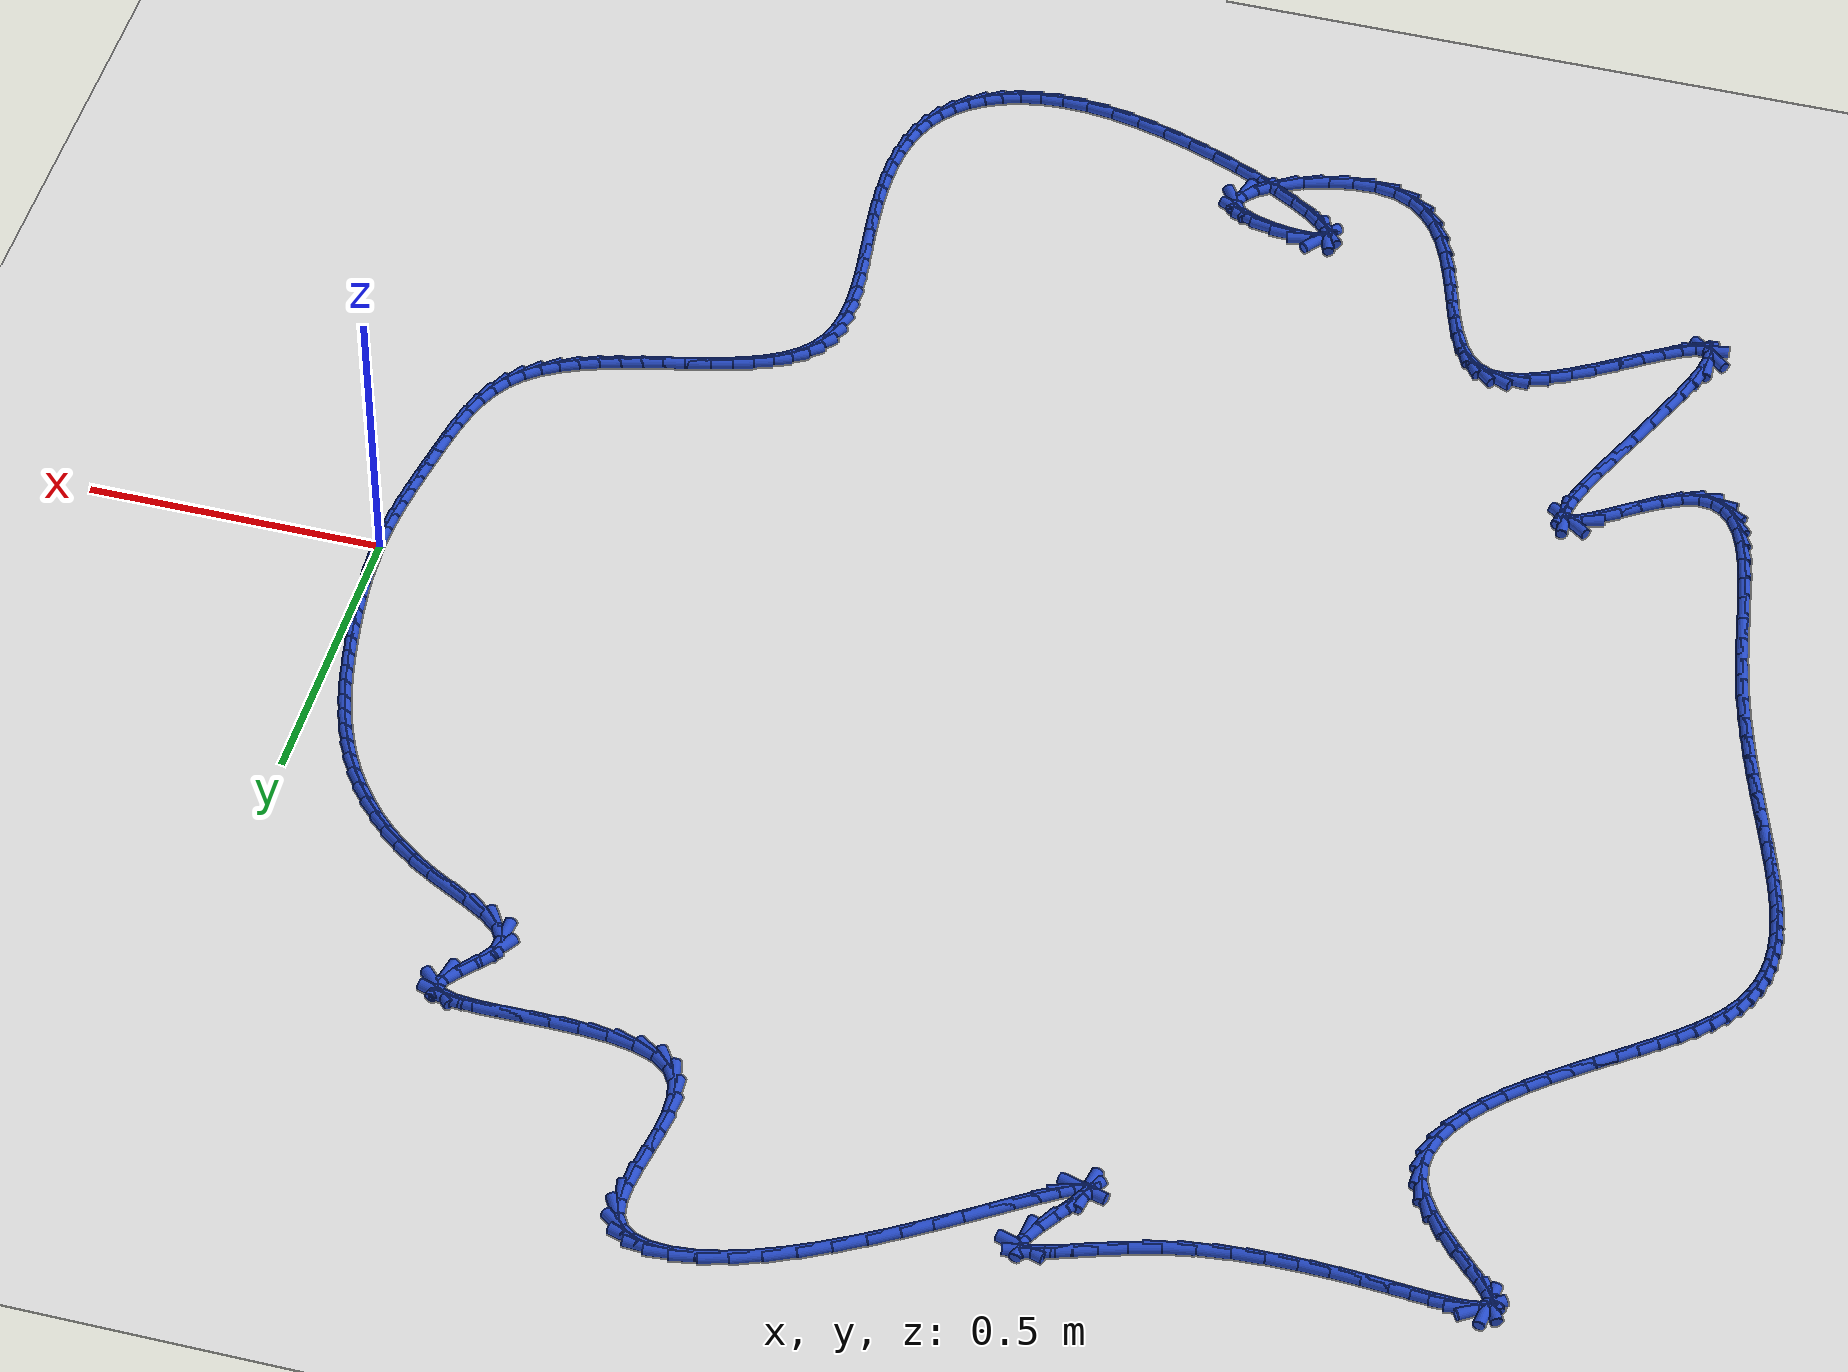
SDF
<sdf version="1.6">
 <world name="default">
  <light name="sun" type="directional">
   <pose>0 0 10 0 -0 0</pose>
   <diffuse>0.8 0.8 0.8 1</diffuse>
   <specular>0.2 0.2 0.2 1</specular>
   <attenuation>
    <range>1000</range>
    <constant>0.9</constant>
    <linear>0.01</linear>
    <quadratic>0.001</quadratic>
   </attenuation>
   <direction>-0.5 0.1 -0.9</direction>
  </light>
  <model name="ground_plane">
   <static>1</static>
   <link name="link">
    <collision name="collision">
     <geometry><plane><normal>0 0 1</normal><size>100 100</size></plane></geometry>
     <surface><friction><ode><mu>100</mu><mu2>50</mu2></ode></friction></surface>
    </collision>
    <visual name="visual">
     <cast_shadows>0</cast_shadows>
     <geometry><plane><normal>0 0 1</normal><size>100 100</size></plane></geometry>
     <material>
      <script><uri>file://media/materials/scripts/gazebo.material</uri><name>Gazebo/WhiteGlow</name></script>
     </material>
    </visual>
   </link>
  </model>
  <gravity>0 0 -9.8</gravity>
  <magnetic_field>6e-06 2.3e-05 -4.2e-05</magnetic_field>
  <atmosphere type="adiabatic"/>
  <physics name="default_physics" default="0" type="ode">
   <max_step_size>0.001</max_step_size>
   <real_time_factor>1</real_time_factor>
   <real_time_update_rate>1000</real_time_update_rate>
  </physics>
  <scene><ambient>0.4 0.4 0.4 1</ambient><background>0.7 0.7 0.7 1</background><shadows>1</shadows></scene>
  <spherical_coordinates>
   <surface_model>EARTH_WGS84</surface_model>
   <latitude_deg>0</latitude_deg>
   <longitude_deg>0</longitude_deg>
   <elevation>0</elevation>
   <heading_deg>0</heading_deg>
  </spherical_coordinates>
  <model name="line">
   <link name="link_0">
    <pose>1.214306433183765e-17 0.0 0.01 0 1.57 -1.5551072129724937</pose>
    <collision name="collision">
     <geometry><cylinder><radius>0.01</radius><length>0.08</length></cylinder></geometry>
    </collision>
    <visual name="visual">
     <material>
      <script><name>Gazebo/Blue</name><uri>file://media/materials/scripts/gazebo.material</uri></script>
     </material>
     <geometry><cylinder><radius>0.01</radius><length>0.08</length></cylinder></geometry>
    </visual>
   </link>
   <link name="link_1">
    <pose>-0.0005051262843972646 0.03219333125570055 0.01 0 1.57 -1.5152921125011434</pose>
    <collision name="collision">
     <geometry><cylinder><radius>0.01</radius><length>0.08</length></cylinder></geometry>
    </collision>
    <visual name="visual">
     <material>
      <script><name>Gazebo/Blue</name><uri>file://media/materials/scripts/gazebo.material</uri></script>
     </material>
     <geometry><cylinder><radius>0.01</radius><length>0.08</length></cylinder></geometry>
    </visual>
   </link>
   <link name="link_2">
    <pose>-0.0023020713427604387 0.06453500852398819 0.01 0 1.57 -1.4802998185177854</pose>
    <collision name="collision">
     <geometry><cylinder><radius>0.01</radius><length>0.08</length></cylinder></geometry>
    </collision>
    <visual name="visual">
     <material>
      <script><name>Gazebo/Blue</name><uri>file://media/materials/scripts/gazebo.material</uri></script>
     </material>
     <geometry><cylinder><radius>0.01</radius><length>0.08</length></cylinder></geometry>
    </visual>
   </link>
   <link name="link_3">
    <pose>-0.005243965689076253 0.09695459041785584 0.01 0 1.57 -1.4498862782628061</pose>
    <collision name="collision">
     <geometry><cylinder><radius>0.01</radius><length>0.08</length></cylinder></geometry>
    </collision>
    <visual name="visual">
     <material>
      <script><name>Gazebo/Blue</name><uri>file://media/materials/scripts/gazebo.material</uri></script>
     </material>
     <geometry><cylinder><radius>0.01</radius><length>0.08</length></cylinder></geometry>
    </visual>
   </link>
   <link name="link_4">
    <pose>-0.009183939837331458 0.12938163555029647 0.01 0 1.57 -1.4238235570488222</pose>
    <collision name="collision">
     <geometry><cylinder><radius>0.01</radius><length>0.08</length></cylinder></geometry>
    </collision>
    <visual name="visual">
     <material>
      <script><name>Gazebo/Blue</name><uri>file://media/materials/scripts/gazebo.material</uri></script>
     </material>
     <geometry><cylinder><radius>0.01</radius><length>0.08</length></cylinder></geometry>
    </visual>
   </link>
   <link name="link_5">
    <pose>-0.013975124301512792 0.161745702534303 0.01 0 1.57 -1.4019142268692817</pose>
    <collision name="collision">
     <geometry><cylinder><radius>0.01</radius><length>0.08</length></cylinder></geometry>
    </collision>
    <visual name="visual">
     <material>
      <script><name>Gazebo/Blue</name><uri>file://media/materials/scripts/gazebo.material</uri></script>
     </material>
     <geometry><cylinder><radius>0.01</radius><length>0.08</length></cylinder></geometry>
    </visual>
   </link>
   <link name="link_6">
    <pose>-0.019470649595607015 0.19397634998286845 0.01 0 1.57 -1.3839388090972564</pose>
    <collision name="collision">
     <geometry><cylinder><radius>0.01</radius><length>0.08</length></cylinder></geometry>
    </collision>
    <visual name="visual">
     <material>
      <script><name>Gazebo/Blue</name><uri>file://media/materials/scripts/gazebo.material</uri></script>
     </material>
     <geometry><cylinder><radius>0.01</radius><length>0.08</length></cylinder></geometry>
    </visual>
   </link>
   <link name="link_7">
    <pose>-0.025525753740951982 0.22600324851694373 0.01 0 1.57 -1.3663174284719959</pose>
    <collision name="collision">
     <geometry><cylinder><radius>0.01</radius><length>0.08</length></cylinder></geometry>
    </collision>
    <visual name="visual">
     <material>
      <script><name>Gazebo/Blue</name><uri>file://media/materials/scripts/gazebo.material</uri></script>
     </material>
     <geometry><cylinder><radius>0.01</radius><length>0.08</length></cylinder></geometry>
    </visual>
   </link>
   <link name="link_8">
    <pose>-0.03211184655908344 0.25776224295474537 0.01 0 1.57 -1.3437445476282743</pose>
    <collision name="collision">
     <geometry><cylinder><radius>0.01</radius><length>0.08</length></cylinder></geometry>
    </collision>
    <visual name="visual">
     <material>
      <script><name>Gazebo/Blue</name><uri>file://media/materials/scripts/gazebo.material</uri></script>
     </material>
     <geometry><cylinder><radius>0.01</radius><length>0.08</length></cylinder></geometry>
    </visual>
   </link>
   <link name="link_9">
    <pose>-0.039374730204036784 0.28919844656570265 0.01 0 1.57 -1.3156919901911617</pose>
    <collision name="collision">
     <geometry><cylinder><radius>0.01</radius><length>0.08</length></cylinder></geometry>
    </collision>
    <visual name="visual">
     <material>
      <script><name>Gazebo/Blue</name><uri>file://media/materials/scripts/gazebo.material</uri></script>
     </material>
     <geometry><cylinder><radius>0.01</radius><length>0.08</length></cylinder></geometry>
    </visual>
   </link>
   <link name="link_10">
    <pose>-0.04747456421903427 0.32025773567321236 0.01 0 1.57 -1.2820834902112814</pose>
    <collision name="collision">
     <geometry><cylinder><radius>0.01</radius><length>0.08</length></cylinder></geometry>
    </collision>
    <visual name="visual">
     <material>
      <script><name>Gazebo/Blue</name><uri>file://media/materials/scripts/gazebo.material</uri></script>
     </material>
     <geometry><cylinder><radius>0.01</radius><length>0.08</length></cylinder></geometry>
    </visual>
   </link>
   <link name="link_11">
    <pose>-0.05657150814729814 0.3508859866006712 0.01 0 1.57 -1.2428923968872843</pose>
    <collision name="collision">
     <geometry><cylinder><radius>0.01</radius><length>0.08</length></cylinder></geometry>
    </collision>
    <visual name="visual">
     <material>
      <script><name>Gazebo/Blue</name><uri>file://media/materials/scripts/gazebo.material</uri></script>
     </material>
     <geometry><cylinder><radius>0.01</radius><length>0.08</length></cylinder></geometry>
    </visual>
   </link>
   <link name="link_12">
    <pose>-0.06682572153205067 0.38102907567147626 0.01 0 1.57 -1.1981735033514036</pose>
    <collision name="collision">
     <geometry><cylinder><radius>0.01</radius><length>0.08</length></cylinder></geometry>
    </collision>
    <visual name="visual">
     <material>
      <script><name>Gazebo/Blue</name><uri>file://media/materials/scripts/gazebo.material</uri></script>
     </material>
     <geometry><cylinder><radius>0.01</radius><length>0.08</length></cylinder></geometry>
    </visual>
   </link>
   <link name="link_13">
    <pose>-0.07839736391651411 0.4106328792090241 0.01 0 1.57 -1.1480985394847345</pose>
    <collision name="collision">
     <geometry><cylinder><radius>0.01</radius><length>0.08</length></cylinder></geometry>
    </collision>
    <visual name="visual">
     <material>
      <script><name>Gazebo/Blue</name><uri>file://media/materials/scripts/gazebo.material</uri></script>
     </material>
     <geometry><cylinder><radius>0.01</radius><length>0.08</length></cylinder></geometry>
    </visual>
   </link>
   <link name="link_14">
    <pose>-0.09144659484391073 0.43964327353671157 0.01 0 1.57 -1.0929911659208689</pose>
    <collision name="collision">
     <geometry><cylinder><radius>0.01</radius><length>0.08</length></cylinder></geometry>
    </collision>
    <visual name="visual">
     <material>
      <script><name>Gazebo/Blue</name><uri>file://media/materials/scripts/gazebo.material</uri></script>
     </material>
     <geometry><cylinder><radius>0.01</radius><length>0.08</length></cylinder></geometry>
    </visual>
   </link>
   <link name="link_15">
    <pose>-0.10613357385746272 0.46800613497793553 0.01 0 1.57 -1.0333549780401643</pose>
    <collision name="collision">
     <geometry><cylinder><radius>0.01</radius><length>0.08</length></cylinder></geometry>
    </collision>
    <visual name="visual">
     <material>
      <script><name>Gazebo/Blue</name><uri>file://media/materials/scripts/gazebo.material</uri></script>
     </material>
     <geometry><cylinder><radius>0.01</radius><length>0.08</length></cylinder></geometry>
    </visual>
   </link>
   <link name="link_16">
    <pose>-0.12261846050039243 0.49566733985609285 0.01 0 1.57 -0.9698864127781095</pose>
    <collision name="collision">
     <geometry><cylinder><radius>0.01</radius><length>0.08</length></cylinder></geometry>
    </collision>
    <visual name="visual">
     <material>
      <script><name>Gazebo/Blue</name><uri>file://media/materials/scripts/gazebo.material</uri></script>
     </material>
     <geometry><cylinder><radius>0.01</radius><length>0.08</length></cylinder></geometry>
    </visual>
   </link>
   <link name="link_17">
    <pose>-0.14106141431592206 0.5225727644945801 0.01 0 1.57 -0.9034648155401545</pose>
    <collision name="collision">
     <geometry><cylinder><radius>0.01</radius><length>0.08</length></cylinder></geometry>
    </collision>
    <visual name="visual">
     <material>
      <script><name>Gazebo/Blue</name><uri>file://media/materials/scripts/gazebo.material</uri></script>
     </material>
     <geometry><cylinder><radius>0.01</radius><length>0.08</length></cylinder></geometry>
    </visual>
   </link>
   <link name="link_18">
    <pose>-0.16162259484727387 0.5486682852167944 0.01 0 1.57 -0.8351152954029909</pose>
    <collision name="collision">
     <geometry><cylinder><radius>0.01</radius><length>0.08</length></cylinder></geometry>
    </collision>
    <visual name="visual">
     <material>
      <script><name>Gazebo/Blue</name><uri>file://media/materials/scripts/gazebo.material</uri></script>
     </material>
     <geometry><cylinder><radius>0.01</radius><length>0.08</length></cylinder></geometry>
    </visual>
   </link>
   <link name="link_19">
    <pose>-0.1844621616376701 0.5738997783461324 0.01 0 1.57 -0.7659462425380974</pose>
    <collision name="collision">
     <geometry><cylinder><radius>0.01</radius><length>0.08</length></cylinder></geometry>
    </collision>
    <visual name="visual">
     <material>
      <script><name>Gazebo/Blue</name><uri>file://media/materials/scripts/gazebo.material</uri></script>
     </material>
     <geometry><cylinder><radius>0.01</radius><length>0.08</length></cylinder></geometry>
    </visual>
   </link>
   <link name="link_20">
    <pose>-0.20974027423033315 0.598213120205991 0.01 0 1.57 -0.6970706329789814</pose>
    <collision name="collision">
     <geometry><cylinder><radius>0.01</radius><length>0.08</length></cylinder></geometry>
    </collision>
    <visual name="visual">
     <material>
      <script><name>Gazebo/Blue</name><uri>file://media/materials/scripts/gazebo.material</uri></script>
     </material>
     <geometry><cylinder><radius>0.01</radius><length>0.08</length></cylinder></geometry>
    </visual>
   </link>
   <link name="link_21">
    <pose>-0.23761709216848506 0.621554187119767 0.01 0 1.57 -0.6295254451600336</pose>
    <collision name="collision">
     <geometry><cylinder><radius>0.01</radius><length>0.08</length></cylinder></geometry>
    </collision>
    <visual name="visual">
     <material>
      <script><name>Gazebo/Blue</name><uri>file://media/materials/scripts/gazebo.material</uri></script>
     </material>
     <geometry><cylinder><radius>0.01</radius><length>0.08</length></cylinder></geometry>
    </visual>
   </link>
   <link name="link_22">
    <pose>-0.2682527749953481 0.6438688554108569 0.01 0 1.57 -0.5642041275196544</pose>
    <collision name="collision">
     <geometry><cylinder><radius>0.01</radius><length>0.08</length></cylinder></geometry>
    </collision>
    <visual name="visual">
     <material>
      <script><name>Gazebo/Blue</name><uri>file://media/materials/scripts/gazebo.material</uri></script>
     </material>
     <geometry><cylinder><radius>0.01</radius><length>0.08</length></cylinder></geometry>
    </visual>
   </link>
   <link name="link_23">
    <pose>-0.30180748225414467 0.665103001402658 0.01 0 1.57 -0.5035021522794236</pose>
    <collision name="collision">
     <geometry><cylinder><radius>0.01</radius><length>0.08</length></cylinder></geometry>
    </collision>
    <visual name="visual">
     <material>
      <script><name>Gazebo/Blue</name><uri>file://media/materials/scripts/gazebo.material</uri></script>
     </material>
     <geometry><cylinder><radius>0.01</radius><length>0.08</length></cylinder></geometry>
    </visual>
   </link>
   <link name="link_24">
    <pose>-0.3383348735912183 0.6852244284133747 0.01 0 1.57 -0.4797698481001998</pose>
    <collision name="collision">
     <geometry><cylinder><radius>0.01</radius><length>0.08</length></cylinder></geometry>
    </collision>
    <visual name="visual">
     <material>
      <script><name>Gazebo/Blue</name><uri>file://media/materials/scripts/gazebo.material</uri></script>
     </material>
     <geometry><cylinder><radius>0.01</radius><length>0.08</length></cylinder></geometry>
    </visual>
   </link>
   <link name="link_25">
    <pose>-0.3756798371373037 0.7046556981504144 0.01 0 1.57 -0.5237333317282393</pose>
    <collision name="collision">
     <geometry><cylinder><radius>0.01</radius><length>0.08</length></cylinder></geometry>
    </collision>
    <visual name="visual">
     <material>
      <script><name>Gazebo/Blue</name><uri>file://media/materials/scripts/gazebo.material</uri></script>
     </material>
     <geometry><cylinder><radius>0.01</radius><length>0.08</length></cylinder></geometry>
    </visual>
   </link>
   <link name="link_26">
    <pose>-0.4096044853300048 0.7242481897486928 0.01 0 1.57 -0.6670960225403552</pose>
    <collision name="collision">
     <geometry><cylinder><radius>0.01</radius><length>0.08</length></cylinder></geometry>
    </collision>
    <visual name="visual">
     <material>
      <script><name>Gazebo/Blue</name><uri>file://media/materials/scripts/gazebo.material</uri></script>
     </material>
     <geometry><cylinder><radius>0.01</radius><length>0.08</length></cylinder></geometry>
    </visual>
   </link>
   <link name="link_27">
    <pose>-0.4357896571292277 0.7448700155341968 0.01 0 1.57 -1.0105385790018424</pose>
    <collision name="collision">
     <geometry><cylinder><radius>0.01</radius><length>0.08</length></cylinder></geometry>
    </collision>
    <visual name="visual">
     <material>
      <script><name>Gazebo/Blue</name><uri>file://media/materials/scripts/gazebo.material</uri></script>
     </material>
     <geometry><cylinder><radius>0.01</radius><length>0.08</length></cylinder></geometry>
    </visual>
   </link>
   <link name="link_28">
    <pose>-0.44991619149487794 0.7673892878329139 0.01 0 1.57 1.4831105472021666</pose>
    <collision name="collision">
     <geometry><cylinder><radius>0.01</radius><length>0.08</length></cylinder></geometry>
    </collision>
    <visual name="visual">
     <material>
      <script><name>Gazebo/Blue</name><uri>file://media/materials/scripts/gazebo.material</uri></script>
     </material>
     <geometry><cylinder><radius>0.01</radius><length>0.08</length></cylinder></geometry>
    </visual>
   </link>
   <link name="link_29">
    <pose>-0.44769405347812974 0.7926663614591976 0.01 0 1.57 0.9899315327982782</pose>
    <collision name="collision">
     <geometry><cylinder><radius>0.01</radius><length>0.08</length></cylinder></geometry>
    </collision>
    <visual name="visual">
     <material>
      <script><name>Gazebo/Blue</name><uri>file://media/materials/scripts/gazebo.material</uri></script>
     </material>
     <geometry><cylinder><radius>0.01</radius><length>0.08</length></cylinder></geometry>
    </visual>
   </link>
   <link name="link_30">
    <pose>-0.42955206669027557 0.8203047593429251 0.01 0 1.57 0.84892931614347</pose>
    <collision name="collision">
     <geometry><cylinder><radius>0.01</radius><length>0.08</length></cylinder></geometry>
    </collision>
    <visual name="visual">
     <material>
      <script><name>Gazebo/Blue</name><uri>file://media/materials/scripts/gazebo.material</uri></script>
     </material>
     <geometry><cylinder><radius>0.01</radius><length>0.08</length></cylinder></geometry>
    </visual>
   </link>
   <link name="link_31">
    <pose>-0.4058090971265108 0.8472738672707357 0.01 0 1.57 0.911341981816925</pose>
    <collision name="collision">
     <geometry><cylinder><radius>0.01</radius><length>0.08</length></cylinder></geometry>
    </collision>
    <visual name="visual">
     <material>
      <script><name>Gazebo/Blue</name><uri>file://media/materials/scripts/gazebo.material</uri></script>
     </material>
     <geometry><cylinder><radius>0.01</radius><length>0.08</length></cylinder></geometry>
    </visual>
   </link>
   <link name="link_32">
    <pose>-0.3880265484437921 0.8702122554823173 0.01 0 1.57 1.3750526792150297</pose>
    <collision name="collision">
     <geometry><cylinder><radius>0.01</radius><length>0.08</length></cylinder></geometry>
    </collision>
    <visual name="visual">
     <material>
      <script><name>Gazebo/Blue</name><uri>file://media/materials/scripts/gazebo.material</uri></script>
     </material>
     <geometry><cylinder><radius>0.01</radius><length>0.08</length></cylinder></geometry>
    </visual>
   </link>
   <link name="link_33">
    <pose>-0.3847471597461507 0.8867512209621835 0.01 0 1.57 -0.7894456864371063</pose>
    <collision name="collision">
     <geometry><cylinder><radius>0.01</radius><length>0.08</length></cylinder></geometry>
    </collision>
    <visual name="visual">
     <material>
      <script><name>Gazebo/Blue</name><uri>file://media/materials/scripts/gazebo.material</uri></script>
     </material>
     <geometry><cylinder><radius>0.01</radius><length>0.08</length></cylinder></geometry>
    </visual>
   </link>
   <link name="link_34">
    <pose>-0.3954213623010875 0.8975121833147218 0.01 0 1.57 -0.2688832324161719</pose>
    <collision name="collision">
     <geometry><cylinder><radius>0.01</radius><length>0.08</length></cylinder></geometry>
    </collision>
    <visual name="visual">
     <material>
      <script><name>Gazebo/Blue</name><uri>file://media/materials/scripts/gazebo.material</uri></script>
     </material>
     <geometry><cylinder><radius>0.01</radius><length>0.08</length></cylinder></geometry>
    </visual>
   </link>
   <link name="link_35">
    <pose>-0.41779460253544365 0.9036772683841723 0.01 0 1.57 -0.08625716387484941</pose>
    <collision name="collision">
     <geometry><cylinder><radius>0.01</radius><length>0.08</length></cylinder></geometry>
    </collision>
    <visual name="visual">
     <material>
      <script><name>Gazebo/Blue</name><uri>file://media/materials/scripts/gazebo.material</uri></script>
     </material>
     <geometry><cylinder><radius>0.01</radius><length>0.08</length></cylinder></geometry>
    </visual>
   </link>
   <link name="link_36">
    <pose>-0.44961232687606045 0.9064286020147739 0.01 0 1.57 -0.013322443763485927</pose>
    <collision name="collision">
     <geometry><cylinder><radius>0.01</radius><length>0.08</length></cylinder></geometry>
    </collision>
    <visual name="visual">
     <material>
      <script><name>Gazebo/Blue</name><uri>file://media/materials/scripts/gazebo.material</uri></script>
     </material>
     <geometry><cylinder><radius>0.01</radius><length>0.08</length></cylinder></geometry>
    </visual>
   </link>
   <link name="link_37">
    <pose>-0.4886199817497788 0.9069483100507664 0.01 0 1.57 0.0120557463879833</pose>
    <collision name="collision">
     <geometry><cylinder><radius>0.01</radius><length>0.08</length></cylinder></geometry>
    </collision>
    <visual name="visual">
     <material>
      <script><name>Gazebo/Blue</name><uri>file://media/materials/scripts/gazebo.material</uri></script>
     </material>
     <geometry><cylinder><radius>0.01</radius><length>0.08</length></cylinder></geometry>
    </visual>
   </link>
   <link name="link_38">
    <pose>-0.5325630135834396 0.9064185183363891 0.01 0 1.57 0.008518300605534806</pose>
    <collision name="collision">
     <geometry><cylinder><radius>0.01</radius><length>0.08</length></cylinder></geometry>
    </collision>
    <visual name="visual">
     <material>
      <script><name>Gazebo/Blue</name><uri>file://media/materials/scripts/gazebo.material</uri></script>
     </material>
     <geometry><cylinder><radius>0.01</radius><length>0.08</length></cylinder></geometry>
    </visual>
   </link>
   <link name="link_39">
    <pose>-0.5791868688038845 0.9060213527158821 0.01 0 1.57 -0.019499842174835396</pose>
    <collision name="collision">
     <geometry><cylinder><radius>0.01</radius><length>0.08</length></cylinder></geometry>
    </collision>
    <visual name="visual">
     <material>
      <script><name>Gazebo/Blue</name><uri>file://media/materials/scripts/gazebo.material</uri></script>
     </material>
     <geometry><cylinder><radius>0.01</radius><length>0.08</length></cylinder></geometry>
    </visual>
   </link>
   <link name="link_40">
    <pose>-0.6262369938379544 0.9069389390334842 0.01 0 1.57 -0.07536176159319098</pose>
    <collision name="collision">
     <geometry><cylinder><radius>0.01</radius><length>0.08</length></cylinder></geometry>
    </collision>
    <visual name="visual">
     <material>
      <script><name>Gazebo/Blue</name><uri>file://media/materials/scripts/gazebo.material</uri></script>
     </material>
     <geometry><cylinder><radius>0.01</radius><length>0.08</length></cylinder></geometry>
    </visual>
   </link>
   <link name="link_41">
    <pose>-0.6714588351124904 0.9103534031334356 0.01 0 1.57 -0.17074786461326713</pose>
    <collision name="collision">
     <geometry><cylinder><radius>0.01</radius><length>0.08</length></cylinder></geometry>
    </collision>
    <visual name="visual">
     <material>
      <script><name>Gazebo/Blue</name><uri>file://media/materials/scripts/gazebo.material</uri></script>
     </material>
     <geometry><cylinder><radius>0.01</radius><length>0.08</length></cylinder></geometry>
    </visual>
   </link>
   <link name="link_42">
    <pose>-0.7125978390543336 0.9174468708599754 0.01 0 1.57 -0.3308787273079353</pose>
    <collision name="collision">
     <geometry><cylinder><radius>0.01</radius><length>0.08</length></cylinder></geometry>
    </collision>
    <visual name="visual">
     <material>
      <script><name>Gazebo/Blue</name><uri>file://media/materials/scripts/gazebo.material</uri></script>
     </material>
     <geometry><cylinder><radius>0.01</radius><length>0.08</length></cylinder></geometry>
    </visual>
   </link>
   <link name="link_43">
    <pose>-0.7473994520903247 0.9294014680573432 0.01 0 1.57 -0.6017263187127433</pose>
    <collision name="collision">
     <geometry><cylinder><radius>0.01</radius><length>0.08</length></cylinder></geometry>
    </collision>
    <visual name="visual">
     <material>
      <script><name>Gazebo/Blue</name><uri>file://media/materials/scripts/gazebo.material</uri></script>
     </material>
     <geometry><cylinder><radius>0.01</radius><length>0.08</length></cylinder></geometry>
    </visual>
   </link>
   <link name="link_44">
    <pose>-0.7736093890145485 0.9473991533755644 0.01 0 1.57 -0.9886532006786259</pose>
    <collision name="collision">
     <geometry><cylinder><radius>0.01</radius><length>0.08</length></cylinder></geometry>
    </collision>
    <visual name="visual">
     <material>
      <script><name>Gazebo/Blue</name><uri>file://media/materials/scripts/gazebo.material</uri></script>
     </material>
     <geometry><cylinder><radius>0.01</radius><length>0.08</length></cylinder></geometry>
    </visual>
   </link>
   <link name="link_45">
    <pose>-0.7898517021059728 0.972074676557782 0.01 0 1.57 -1.3203665644300926</pose>
    <collision name="collision">
     <geometry><cylinder><radius>0.01</radius><length>0.08</length></cylinder></geometry>
    </collision>
    <visual name="visual">
     <material>
      <script><name>Gazebo/Blue</name><uri>file://media/materials/scripts/gazebo.material</uri></script>
     </material>
     <geometry><cylinder><radius>0.01</radius><length>0.08</length></cylinder></geometry>
    </visual>
   </link>
   <link name="link_46">
    <pose>-0.7975828652404875 1.0022981736849026 0.01 0 1.57 -1.534461543025685</pose>
    <collision name="collision">
     <geometry><cylinder><radius>0.01</radius><length>0.08</length></cylinder></geometry>
    </collision>
    <visual name="visual">
     <material>
      <script><name>Gazebo/Blue</name><uri>file://media/materials/scripts/gazebo.material</uri></script>
     </material>
     <geometry><cylinder><radius>0.01</radius><length>0.08</length></cylinder></geometry>
    </visual>
   </link>
   <link name="link_47">
    <pose>-0.7988292093562954 1.0365847568686712 0.01 0 1.57 1.4838827031104111</pose>
    <collision name="collision">
     <geometry><cylinder><radius>0.01</radius><length>0.08</length></cylinder></geometry>
    </collision>
    <visual name="visual">
     <material>
      <script><name>Gazebo/Blue</name><uri>file://media/materials/scripts/gazebo.material</uri></script>
     </material>
     <geometry><cylinder><radius>0.01</radius><length>0.08</length></cylinder></geometry>
    </visual>
   </link>
   <link name="link_48">
    <pose>-0.7956170653915993 1.0734495382208322 0.01 0 1.57 1.4231797446355212</pose>
    <collision name="collision">
     <geometry><cylinder><radius>0.01</radius><length>0.08</length></cylinder></geometry>
    </collision>
    <visual name="visual">
     <material>
      <script><name>Gazebo/Blue</name><uri>file://media/materials/scripts/gazebo.material</uri></script>
     </material>
     <geometry><cylinder><radius>0.01</radius><length>0.08</length></cylinder></geometry>
    </visual>
   </link>
   <link name="link_49">
    <pose>-0.7899727642846015 1.1114076298531304 0.01 0 1.57 1.4111163979288632</pose>
    <collision name="collision">
     <geometry><cylinder><radius>0.01</radius><length>0.08</length></cylinder></geometry>
    </collision>
    <visual name="visual">
     <material>
      <script><name>Gazebo/Blue</name><uri>file://media/materials/scripts/gazebo.material</uri></script>
     </material>
     <geometry><cylinder><radius>0.01</radius><length>0.08</length></cylinder></geometry>
    </visual>
   </link>
   <link name="link_50">
    <pose>-0.7839226369735051 1.1489741438773104 0.01 0 1.57 1.4473141304484487</pose>
    <collision name="collision">
     <geometry><cylinder><radius>0.01</radius><length>0.08</length></cylinder></geometry>
    </collision>
    <visual name="visual">
     <material>
      <script><name>Gazebo/Blue</name><uri>file://media/materials/scripts/gazebo.material</uri></script>
     </material>
     <geometry><cylinder><radius>0.01</radius><length>0.08</length></cylinder></geometry>
    </visual>
   </link>
   <link name="link_51">
    <pose>-0.7794930143965126 1.184664192405117 0.01 0 1.57 1.546587679474687</pose>
    <collision name="collision">
     <geometry><cylinder><radius>0.01</radius><length>0.08</length></cylinder></geometry>
    </collision>
    <visual name="visual">
     <material>
      <script><name>Gazebo/Blue</name><uri>file://media/materials/scripts/gazebo.material</uri></script>
     </material>
     <geometry><cylinder><radius>0.01</radius><length>0.08</length></cylinder></geometry>
    </visual>
   </link>
   <link name="link_52">
    <pose>-0.7787102274918267 1.2169928875482952 0.01 0 1.57 -1.3946940972062774</pose>
    <collision name="collision">
     <geometry><cylinder><radius>0.01</radius><length>0.08</length></cylinder></geometry>
    </collision>
    <visual name="visual">
     <material>
      <script><name>Gazebo/Blue</name><uri>file://media/materials/scripts/gazebo.material</uri></script>
     </material>
     <geometry><cylinder><radius>0.01</radius><length>0.08</length></cylinder></geometry>
    </visual>
   </link>
   <link name="link_53">
    <pose>-0.7836006071976497 1.244475341418589 0.01 0 1.57 -1.0379626142749292</pose>
    <collision name="collision">
     <geometry><cylinder><radius>0.01</radius><length>0.08</length></cylinder></geometry>
    </collision>
    <visual name="visual">
     <material>
      <script><name>Gazebo/Blue</name><uri>file://media/materials/scripts/gazebo.material</uri></script>
     </material>
     <geometry><cylinder><radius>0.01</radius><length>0.08</length></cylinder></geometry>
    </visual>
   </link>
   <link name="link_54">
    <pose>-0.7961042457244494 1.265677656306789 0.01 0 1.57 -0.6138053453899145</pose>
    <collision name="collision">
     <geometry><cylinder><radius>0.01</radius><length>0.08</length></cylinder></geometry>
    </collision>
    <visual name="visual">
     <material>
      <script><name>Gazebo/Blue</name><uri>file://media/materials/scripts/gazebo.material</uri></script>
     </material>
     <geometry><cylinder><radius>0.01</radius><length>0.08</length></cylinder></geometry>
    </visual>
   </link>
   <link name="link_55">
    <pose>-0.8165769379141731 1.2801026784539085 0.01 0 1.57 -0.28307058510540345</pose>
    <collision name="collision">
     <geometry><cylinder><radius>0.01</radius><length>0.08</length></cylinder></geometry>
    </collision>
    <visual name="visual">
     <material>
      <script><name>Gazebo/Blue</name><uri>file://media/materials/scripts/gazebo.material</uri></script>
     </material>
     <geometry><cylinder><radius>0.01</radius><length>0.08</length></cylinder></geometry>
    </visual>
   </link>
   <link name="link_56">
    <pose>-0.8439845740586148 1.2880750598456512 0.01 0 1.57 -0.056230418537408726</pose>
    <collision name="collision">
     <geometry><cylinder><radius>0.01</radius><length>0.08</length></cylinder></geometry>
    </collision>
    <visual name="visual">
     <material>
      <script><name>Gazebo/Blue</name><uri>file://media/materials/scripts/gazebo.material</uri></script>
     </material>
     <geometry><cylinder><radius>0.01</radius><length>0.08</length></cylinder></geometry>
    </visual>
   </link>
   <link name="link_57">
    <pose>-0.8772458932559423 1.289947331448176 0.01 0 1.57 0.10154087060811326</pose>
    <collision name="collision">
     <geometry><cylinder><radius>0.01</radius><length>0.08</length></cylinder></geometry>
    </collision>
    <visual name="visual">
     <material>
      <script><name>Gazebo/Blue</name><uri>file://media/materials/scripts/gazebo.material</uri></script>
     </material>
     <geometry><cylinder><radius>0.01</radius><length>0.08</length></cylinder></geometry>
    </visual>
   </link>
   <link name="link_58">
    <pose>-0.915279634604323 1.2860720242276447 0.01 0 1.57 0.21862679672249244</pose>
    <collision name="collision">
     <geometry><cylinder><radius>0.01</radius><length>0.08</length></cylinder></geometry>
    </collision>
    <visual name="visual">
     <material>
      <script><name>Gazebo/Blue</name><uri>file://media/materials/scripts/gazebo.material</uri></script>
     </material>
     <geometry><cylinder><radius>0.01</radius><length>0.08</length></cylinder></geometry>
    </visual>
   </link>
   <link name="link_59">
    <pose>-0.9570045372019248 1.2768016691502175 0.01 0 1.57 0.3122732990493578</pose>
    <collision name="collision">
     <geometry><cylinder><radius>0.01</radius><length>0.08</length></cylinder></geometry>
    </collision>
    <visual name="visual">
     <material>
      <script><name>Gazebo/Blue</name><uri>file://media/materials/scripts/gazebo.material</uri></script>
     </material>
     <geometry><cylinder><radius>0.01</radius><length>0.08</length></cylinder></geometry>
    </visual>
   </link>
   <link name="link_60">
    <pose>-1.0013393429118043 1.2624888023531644 0.01 0 1.57 0.3901425774062699</pose>
    <collision name="collision">
     <geometry><cylinder><radius>0.01</radius><length>0.08</length></cylinder></geometry>
    </collision>
    <visual name="visual">
     <material>
      <script><name>Gazebo/Blue</name><uri>file://media/materials/scripts/gazebo.material</uri></script>
     </material>
     <geometry><cylinder><radius>0.01</radius><length>0.08</length></cylinder></geometry>
    </visual>
   </link>
   <link name="link_61">
    <pose>-1.047265384507908 1.2436030223640375 0.01 0 1.57 0.44999594107570073</pose>
    <collision name="collision">
     <geometry><cylinder><radius>0.01</radius><length>0.08</length></cylinder></geometry>
    </collision>
    <visual name="visual">
     <material>
      <script><name>Gazebo/Blue</name><uri>file://media/materials/scripts/gazebo.material</uri></script>
     </material>
     <geometry><cylinder><radius>0.01</radius><length>0.08</length></cylinder></geometry>
    </visual>
   </link>
   <link name="link_62">
    <pose>-1.0939883316323495 1.2210334999716461 0.01 0 1.57 0.4953188959967603</pose>
    <collision name="collision">
     <geometry><cylinder><radius>0.01</radius><length>0.08</length></cylinder></geometry>
    </collision>
    <visual name="visual">
     <material>
      <script><name>Gazebo/Blue</name><uri>file://media/materials/scripts/gazebo.material</uri></script>
     </material>
     <geometry><cylinder><radius>0.01</radius><length>0.08</length></cylinder></geometry>
    </visual>
   </link>
   <link name="link_63">
    <pose>-1.1407640953341134 1.1957633713520346 0.01 0 1.57 0.5297723828528761</pose>
    <collision name="collision">
     <geometry><cylinder><radius>0.01</radius><length>0.08</length></cylinder></geometry>
    </collision>
    <visual name="visual">
     <material>
      <script><name>Gazebo/Blue</name><uri>file://media/materials/scripts/gazebo.material</uri></script>
     </material>
     <geometry><cylinder><radius>0.01</radius><length>0.08</length></cylinder></geometry>
    </visual>
   </link>
   <link name="link_64">
    <pose>-1.1868485866621818 1.1687757726812475 0.01 0 1.57 0.5556340524834525</pose>
    <collision name="collision">
     <geometry><cylinder><radius>0.01</radius><length>0.08</length></cylinder></geometry>
    </collision>
    <visual name="visual">
     <material>
      <script><name>Gazebo/Blue</name><uri>file://media/materials/scripts/gazebo.material</uri></script>
     </material>
     <geometry><cylinder><radius>0.01</radius><length>0.08</length></cylinder></geometry>
    </visual>
   </link>
   <link name="link_65">
    <pose>-1.2314977166655388 1.1410538401353305 0.01 0 1.57 0.5741844785211364</pose>
    <collision name="collision">
     <geometry><cylinder><radius>0.01</radius><length>0.08</length></cylinder></geometry>
    </collision>
    <visual name="visual">
     <material>
      <script><name>Gazebo/Blue</name><uri>file://media/materials/scripts/gazebo.material</uri></script>
     </material>
     <geometry><cylinder><radius>0.01</radius><length>0.08</length></cylinder></geometry>
    </visual>
   </link>
   <link name="link_66">
    <pose>-1.273967396393168 1.1135807098903276 0.01 0 1.57 0.5858479553913527</pose>
    <collision name="collision">
     <geometry><cylinder><radius>0.01</radius><length>0.08</length></cylinder></geometry>
    </collision>
    <visual name="visual">
     <material>
      <script><name>Gazebo/Blue</name><uri>file://media/materials/scripts/gazebo.material</uri></script>
     </material>
     <geometry><cylinder><radius>0.01</radius><length>0.08</length></cylinder></geometry>
    </visual>
   </link>
   <link name="link_67">
    <pose>-1.313513536894052 1.087339518122285 0.01 0 1.57 0.590066518010081</pose>
    <collision name="collision">
     <geometry><cylinder><radius>0.01</radius><length>0.08</length></cylinder></geometry>
    </collision>
    <visual name="visual">
     <material>
      <script><name>Gazebo/Blue</name><uri>file://media/materials/scripts/gazebo.material</uri></script>
     </material>
     <geometry><cylinder><radius>0.01</radius><length>0.08</length></cylinder></geometry>
    </visual>
   </link>
   <link name="link_68">
    <pose>-1.349392049217175 1.0633134010072458 0.01 0 1.57 0.5846961030180268</pose>
    <collision name="collision">
     <geometry><cylinder><radius>0.01</radius><length>0.08</length></cylinder></geometry>
    </collision>
    <visual name="visual">
     <material>
      <script><name>Gazebo/Blue</name><uri>file://media/materials/scripts/gazebo.material</uri></script>
     </material>
     <geometry><cylinder><radius>0.01</radius><length>0.08</length></cylinder></geometry>
    </visual>
   </link>
   <link name="link_69">
    <pose>-1.3808588444115197 1.0424854947212565 0.01 0 1.57 0.5641062893892069</pose>
    <collision name="collision">
     <geometry><cylinder><radius>0.01</radius><length>0.08</length></cylinder></geometry>
    </collision>
    <visual name="visual">
     <material>
      <script><name>Gazebo/Blue</name><uri>file://media/materials/scripts/gazebo.material</uri></script>
     </material>
     <geometry><cylinder><radius>0.01</radius><length>0.08</length></cylinder></geometry>
    </visual>
   </link>
   <link name="link_70">
    <pose>-1.407169833526071 1.0258389354403619 0.01 0 1.57 0.5124205613549347</pose>
    <collision name="collision">
     <geometry><cylinder><radius>0.01</radius><length>0.08</length></cylinder></geometry>
    </collision>
    <visual name="visual">
     <material>
      <script><name>Gazebo/Blue</name><uri>file://media/materials/scripts/gazebo.material</uri></script>
     </material>
     <geometry><cylinder><radius>0.01</radius><length>0.08</length></cylinder></geometry>
    </visual>
   </link>
   <link name="link_71">
    <pose>-1.4275809276098108 1.0143568593406058 0.01 0 1.57 0.36966544214115243</pose>
    <collision name="collision">
     <geometry><cylinder><radius>0.01</radius><length>0.08</length></cylinder></geometry>
    </collision>
    <visual name="visual">
     <material>
      <script><name>Gazebo/Blue</name><uri>file://media/materials/scripts/gazebo.material</uri></script>
     </material>
     <geometry><cylinder><radius>0.01</radius><length>0.08</length></cylinder></geometry>
    </visual>
   </link>
   <link name="link_72">
    <pose>-1.441348037711723 1.0090224025980339 0.01 0 1.57 -0.27448623500930663</pose>
    <collision name="collision">
     <geometry><cylinder><radius>0.01</radius><length>0.08</length></cylinder></geometry>
    </collision>
    <visual name="visual">
     <material>
      <script><name>Gazebo/Blue</name><uri>file://media/materials/scripts/gazebo.material</uri></script>
     </material>
     <geometry><cylinder><radius>0.01</radius><length>0.08</length></cylinder></geometry>
    </visual>
   </link>
   <link name="link_73">
    <pose>-1.4477270748807913 1.010818701388691 0.01 0 1.57 1.3957065398257538</pose>
    <collision name="collision">
     <geometry><cylinder><radius>0.01</radius><length>0.08</length></cylinder></geometry>
    </collision>
    <visual name="visual">
     <material>
      <script><name>Gazebo/Blue</name><uri>file://media/materials/scripts/gazebo.material</uri></script>
     </material>
     <geometry><cylinder><radius>0.01</radius><length>0.08</length></cylinder></geometry>
    </visual>
   </link>
   <link name="link_74">
    <pose>-1.4459739501659992 1.0207288918886221 0.01 0 1.57 1.060895622629085</pose>
    <collision name="collision">
     <geometry><cylinder><radius>0.01</radius><length>0.08</length></cylinder></geometry>
    </collision>
    <visual name="visual">
     <material>
      <script><name>Gazebo/Blue</name><uri>file://media/materials/scripts/gazebo.material</uri></script>
     </material>
     <geometry><cylinder><radius>0.01</radius><length>0.08</length></cylinder></geometry>
    </visual>
   </link>
   <link name="link_75">
    <pose>-1.4353445746163296 1.039736110273872 0.01 0 1.57 0.9737874297250769</pose>
    <collision name="collision">
     <geometry><cylinder><radius>0.01</radius><length>0.08</length></cylinder></geometry>
    </collision>
    <visual name="visual">
     <material>
      <script><name>Gazebo/Blue</name><uri>file://media/materials/scripts/gazebo.material</uri></script>
     </material>
     <geometry><cylinder><radius>0.01</radius><length>0.08</length></cylinder></geometry>
    </visual>
   </link>
   <link name="link_76">
    <pose>-1.4164477400136493 1.0675356014170758 0.01 0 1.57 0.9764831523756357</pose>
    <collision name="collision">
     <geometry><cylinder><radius>0.01</radius><length>0.08</length></cylinder></geometry>
    </collision>
    <visual name="visual">
     <material>
      <script><name>Gazebo/Blue</name><uri>file://media/materials/scripts/gazebo.material</uri></script>
     </material>
     <geometry><cylinder><radius>0.01</radius><length>0.08</length></cylinder></geometry>
    </visual>
   </link>
   <link name="link_77">
    <pose>-1.395589776482752 1.0983987691202242 0.01 0 1.57 1.0596949639302038</pose>
    <collision name="collision">
     <geometry><cylinder><radius>0.01</radius><length>0.08</length></cylinder></geometry>
    </collision>
    <visual name="visual">
     <material>
      <script><name>Gazebo/Blue</name><uri>file://media/materials/scripts/gazebo.material</uri></script>
     </material>
     <geometry><cylinder><radius>0.01</radius><length>0.08</length></cylinder></geometry>
    </visual>
   </link>
   <link name="link_78">
    <pose>-1.3805766416713932 1.1251694284864409 0.01 0 1.57 1.4565418072173917</pose>
    <collision name="collision">
     <geometry><cylinder><radius>0.01</radius><length>0.08</length></cylinder></geometry>
    </collision>
    <visual name="visual">
     <material>
      <script><name>Gazebo/Blue</name><uri>file://media/materials/scripts/gazebo.material</uri></script>
     </material>
     <geometry><cylinder><radius>0.01</radius><length>0.08</length></cylinder></geometry>
    </visual>
   </link>
   <link name="link_79">
    <pose>-1.3787428368249641 1.1411497008272657 0.01 0 1.57 -0.309898226240471</pose>
    <collision name="collision">
     <geometry><cylinder><radius>0.01</radius><length>0.08</length></cylinder></geometry>
    </collision>
    <visual name="visual">
     <material>
      <script><name>Gazebo/Blue</name><uri>file://media/materials/scripts/gazebo.material</uri></script>
     </material>
     <geometry><cylinder><radius>0.01</radius><length>0.08</length></cylinder></geometry>
    </visual>
   </link>
   <link name="link_80">
    <pose>-1.3916273866377389 1.1452755307078553 0.01 0 1.57 0.19578130825143006</pose>
    <collision name="collision">
     <geometry><cylinder><radius>0.01</radius><length>0.08</length></cylinder></geometry>
    </collision>
    <visual name="visual">
     <material>
      <script><name>Gazebo/Blue</name><uri>file://media/materials/scripts/gazebo.material</uri></script>
     </material>
     <geometry><cylinder><radius>0.01</radius><length>0.08</length></cylinder></geometry>
    </visual>
   </link>
   <link name="link_81">
    <pose>-1.4168752244383929 1.1402683361214299 0.01 0 1.57 0.31201529950717044</pose>
    <collision name="collision">
     <geometry><cylinder><radius>0.01</radius><length>0.08</length></cylinder></geometry>
    </collision>
    <visual name="visual">
     <material>
      <script><name>Gazebo/Blue</name><uri>file://media/materials/scripts/gazebo.material</uri></script>
     </material>
     <geometry><cylinder><radius>0.01</radius><length>0.08</length></cylinder></geometry>
    </visual>
   </link>
   <link name="link_82">
    <pose>-1.4520590452879973 1.128919758385942 0.01 0 1.57 0.33575522227409255</pose>
    <collision name="collision">
     <geometry><cylinder><radius>0.01</radius><length>0.08</length></cylinder></geometry>
    </collision>
    <visual name="visual">
     <material>
      <script><name>Gazebo/Blue</name><uri>file://media/materials/scripts/gazebo.material</uri></script>
     </material>
     <geometry><cylinder><radius>0.01</radius><length>0.08</length></cylinder></geometry>
    </visual>
   </link>
   <link name="link_83">
    <pose>-1.494751544247624 1.1140214388193455 0.01 0 1.57 0.31668944633849033</pose>
    <collision name="collision">
     <geometry><cylinder><radius>0.01</radius><length>0.08</length></cylinder></geometry>
    </collision>
    <visual name="visual">
     <material>
      <script><name>Gazebo/Blue</name><uri>file://media/materials/scripts/gazebo.material</uri></script>
     </material>
     <geometry><cylinder><radius>0.01</radius><length>0.08</length></cylinder></geometry>
    </visual>
   </link>
   <link name="link_84">
    <pose>-1.5425254163783444 1.0983650187395932 0.01 0 1.57 0.26391288006326485</pose>
    <collision name="collision">
     <geometry><cylinder><radius>0.01</radius><length>0.08</length></cylinder></geometry>
    </collision>
    <visual name="visual">
     <material>
      <script><name>Gazebo/Blue</name><uri>file://media/materials/scripts/gazebo.material</uri></script>
     </material>
     <geometry><cylinder><radius>0.01</radius><length>0.08</length></cylinder></geometry>
    </visual>
   </link>
   <link name="link_85">
    <pose>-1.5929555509627307 1.0847380039390737 0.01 0 1.57 0.18839973131292334</pose>
    <collision name="collision">
     <geometry><cylinder><radius>0.01</radius><length>0.08</length></cylinder></geometry>
    </collision>
    <visual name="visual">
     <material>
      <script><name>Gazebo/Blue</name><uri>file://media/materials/scripts/gazebo.material</uri></script>
     </material>
     <geometry><cylinder><radius>0.01</radius><length>0.08</length></cylinder></geometry>
    </visual>
   </link>
   <link name="link_86">
    <pose>-1.6441180091431447 1.0749833241786566 0.01 0 1.57 0.1203615236274353</pose>
    <collision name="collision">
     <geometry><cylinder><radius>0.01</radius><length>0.08</length></cylinder></geometry>
    </collision>
    <visual name="visual">
     <material>
      <script><name>Gazebo/Blue</name><uri>file://media/materials/scripts/gazebo.material</uri></script>
     </material>
     <geometry><cylinder><radius>0.01</radius><length>0.08</length></cylinder></geometry>
    </visual>
   </link>
   <link name="link_87">
    <pose>-1.6952252497103972 1.0688021010549384 0.01 0 1.57 0.06341687578810595</pose>
    <collision name="collision">
     <geometry><cylinder><radius>0.01</radius><length>0.08</length></cylinder></geometry>
    </collision>
    <visual name="visual">
     <material>
      <script><name>Gazebo/Blue</name><uri>file://media/materials/scripts/gazebo.material</uri></script>
     </material>
     <geometry><cylinder><radius>0.01</radius><length>0.08</length></cylinder></geometry>
    </visual>
   </link>
   <link name="link_88">
    <pose>-1.7456463570175456 1.065600258520966 0.01 0 1.57 0.016627194751597265</pose>
    <collision name="collision">
     <geometry><cylinder><radius>0.01</radius><length>0.08</length></cylinder></geometry>
    </collision>
    <visual name="visual">
     <material>
      <script><name>Gazebo/Blue</name><uri>file://media/materials/scripts/gazebo.material</uri></script>
     </material>
     <geometry><cylinder><radius>0.01</radius><length>0.08</length></cylinder></geometry>
    </visual>
   </link>
   <link name="link_89">
    <pose>-1.7947504154176481 1.0647837205297879 0.01 0 1.57 -0.020666506835584502</pose>
    <collision name="collision">
     <geometry><cylinder><radius>0.01</radius><length>0.08</length></cylinder></geometry>
    </collision>
    <visual name="visual">
     <material>
      <script><name>Gazebo/Blue</name><uri>file://media/materials/scripts/gazebo.material</uri></script>
     </material>
     <geometry><cylinder><radius>0.01</radius><length>0.08</length></cylinder></geometry>
    </visual>
   </link>
   <link name="link_90">
    <pose>-1.8419065092637623 1.0657584110344511 0.01 0 1.57 -0.048682426837604285</pose>
    <collision name="collision">
     <geometry><cylinder><radius>0.01</radius><length>0.08</length></cylinder></geometry>
    </collision>
    <visual name="visual">
     <material>
      <script><name>Gazebo/Blue</name><uri>file://media/materials/scripts/gazebo.material</uri></script>
     </material>
     <geometry><cylinder><radius>0.01</radius><length>0.08</length></cylinder></geometry>
    </visual>
   </link>
   <link name="link_91">
    <pose>-1.886483722908946 1.0679302539880036 0.01 0 1.57 -0.06697948770084197</pose>
    <collision name="collision">
     <geometry><cylinder><radius>0.01</radius><length>0.08</length></cylinder></geometry>
    </collision>
    <visual name="visual">
     <material>
      <script><name>Gazebo/Blue</name><uri>file://media/materials/scripts/gazebo.material</uri></script>
     </material>
     <geometry><cylinder><radius>0.01</radius><length>0.08</length></cylinder></geometry>
    </visual>
   </link>
   <link name="link_92">
    <pose>-1.9278511407062564 1.0707051733434925 0.01 0 1.57 -0.0740493839488016</pose>
    <collision name="collision">
     <geometry><cylinder><radius>0.01</radius><length>0.08</length></cylinder></geometry>
    </collision>
    <visual name="visual">
     <material>
      <script><name>Gazebo/Blue</name><uri>file://media/materials/scripts/gazebo.material</uri></script>
     </material>
     <geometry><cylinder><radius>0.01</radius><length>0.08</length></cylinder></geometry>
    </visual>
   </link>
   <link name="link_93">
    <pose>-1.9653778470087522 1.0734890930539662 0.01 0 1.57 -0.06642275164176134</pose>
    <collision name="collision">
     <geometry><cylinder><radius>0.01</radius><length>0.08</length></cylinder></geometry>
    </collision>
    <visual name="visual">
     <material>
      <script><name>Gazebo/Blue</name><uri>file://media/materials/scripts/gazebo.material</uri></script>
     </material>
     <geometry><cylinder><radius>0.01</radius><length>0.08</length></cylinder></geometry>
    </visual>
   </link>
   <link name="link_94">
    <pose>-1.998432926169491 1.0756879370724723 0.01 0 1.57 -0.03646325002539953</pose>
    <collision name="collision">
     <geometry><cylinder><radius>0.01</radius><length>0.08</length></cylinder></geometry>
    </collision>
    <visual name="visual">
     <material>
      <script><name>Gazebo/Blue</name><uri>file://media/materials/scripts/gazebo.material</uri></script>
     </material>
     <geometry><cylinder><radius>0.01</radius><length>0.08</length></cylinder></geometry>
    </visual>
   </link>
   <link name="link_95">
    <pose>-2.026385462541532 1.0767076293520585 0.01 0 1.57 0.03390090327300626</pose>
    <collision name="collision">
     <geometry><cylinder><radius>0.01</radius><length>0.08</length></cylinder></geometry>
    </collision>
    <visual name="visual">
     <material>
      <script><name>Gazebo/Blue</name><uri>file://media/materials/scripts/gazebo.material</uri></script>
     </material>
     <geometry><cylinder><radius>0.01</radius><length>0.08</length></cylinder></geometry>
    </visual>
   </link>
   <link name="link_96">
    <pose>-2.048604540477931 1.0759540938457721 0.01 0 1.57 0.1943552256495177</pose>
    <collision name="collision">
     <geometry><cylinder><radius>0.01</radius><length>0.08</length></cylinder></geometry>
    </collision>
    <visual name="visual">
     <material>
      <script><name>Gazebo/Blue</name><uri>file://media/materials/scripts/gazebo.material</uri></script>
     </material>
     <geometry><cylinder><radius>0.01</radius><length>0.08</length></cylinder></geometry>
    </visual>
   </link>
   <link name="link_97">
    <pose>-2.0644592443317458 1.072833254506661 0.01 0 1.57 0.601625738121306</pose>
    <collision name="collision">
     <geometry><cylinder><radius>0.01</radius><length>0.08</length></cylinder></geometry>
    </collision>
    <visual name="visual">
     <material>
      <script><name>Gazebo/Blue</name><uri>file://media/materials/scripts/gazebo.material</uri></script>
     </material>
     <geometry><cylinder><radius>0.01</radius><length>0.08</length></cylinder></geometry>
    </visual>
   </link>
   <link name="link_98">
    <pose>-2.0733186584560355 1.0667510352877727 0.01 0 1.57 1.4435308155119944</pose>
    <collision name="collision">
     <geometry><cylinder><radius>0.01</radius><length>0.08</length></cylinder></geometry>
    </collision>
    <visual name="visual">
     <material>
      <script><name>Gazebo/Blue</name><uri>file://media/materials/scripts/gazebo.material</uri></script>
     </material>
     <geometry><cylinder><radius>0.01</radius><length>0.08</length></cylinder></geometry>
    </visual>
   </link>
   <link name="link_99">
    <pose>-2.0745518672038576 1.0571133601421554 0.01 0 1.57 -1.099742794856871</pose>
    <collision name="collision">
     <geometry><cylinder><radius>0.01</radius><length>0.08</length></cylinder></geometry>
    </collision>
    <visual name="visual">
     <material>
      <script><name>Gazebo/Blue</name><uri>file://media/materials/scripts/gazebo.material</uri></script>
     </material>
     <geometry><cylinder><radius>0.01</radius><length>0.08</length></cylinder></geometry>
    </visual>
   </link>
   <link name="link_100">
    <pose>-2.0675307573712 1.043327339374024 0.01 0 1.57 -0.8786188223495467</pose>
    <collision name="collision">
     <geometry><cylinder><radius>0.01</radius><length>0.08</length></cylinder></geometry>
    </collision>
    <visual name="visual">
     <material>
      <script><name>Gazebo/Blue</name><uri>file://media/materials/scripts/gazebo.material</uri></script>
     </material>
     <geometry><cylinder><radius>0.01</radius><length>0.08</length></cylinder></geometry>
    </visual>
   </link>
   <link name="link_101">
    <pose>-2.0524659392258813 1.025155138000584 0.01 0 1.57 -0.8100609833291657</pose>
    <collision name="collision">
     <geometry><cylinder><radius>0.01</radius><length>0.08</length></cylinder></geometry>
    </collision>
    <visual name="visual">
     <material>
      <script><name>Gazebo/Blue</name><uri>file://media/materials/scripts/gazebo.material</uri></script>
     </material>
     <geometry><cylinder><radius>0.01</radius><length>0.08</length></cylinder></geometry>
    </visual>
   </link>
   <link name="link_102">
    <pose>-2.03157669961105 1.0032092490778939 0.01 0 1.57 -0.8013070545493701</pose>
    <collision name="collision">
     <geometry><cylinder><radius>0.01</radius><length>0.08</length></cylinder></geometry>
    </collision>
    <visual name="visual">
     <material>
      <script><name>Gazebo/Blue</name><uri>file://media/materials/scripts/gazebo.material</uri></script>
     </material>
     <geometry><cylinder><radius>0.01</radius><length>0.08</length></cylinder></geometry>
    </visual>
   </link>
   <link name="link_103">
    <pose>-2.007376762720257 0.9782268090903321 0.01 0 1.57 -0.8290772997848959</pose>
    <collision name="collision">
     <geometry><cylinder><radius>0.01</radius><length>0.08</length></cylinder></geometry>
    </collision>
    <visual name="visual">
     <material>
      <script><name>Gazebo/Blue</name><uri>file://media/materials/scripts/gazebo.material</uri></script>
     </material>
     <geometry><cylinder><radius>0.01</radius><length>0.08</length></cylinder></geometry>
    </visual>
   </link>
   <link name="link_104">
    <pose>-1.9823798527470535 0.9509449545222765 0.01 0 1.57 -0.8917398385609193</pose>
    <collision name="collision">
     <geometry><cylinder><radius>0.01</radius><length>0.08</length></cylinder></geometry>
    </collision>
    <visual name="visual">
     <material>
      <script><name>Gazebo/Blue</name><uri>file://media/materials/scripts/gazebo.material</uri></script>
     </material>
     <geometry><cylinder><radius>0.01</radius><length>0.08</length></cylinder></geometry>
    </visual>
   </link>
   <link name="link_105">
    <pose>-1.959099693884991 0.922100821858105 0.01 0 1.57 -1.0000176219292862</pose>
    <collision name="collision">
     <geometry><cylinder><radius>0.01</radius><length>0.08</length></cylinder></geometry>
    </collision>
    <visual name="visual">
     <material>
      <script><name>Gazebo/Blue</name><uri>file://media/materials/scripts/gazebo.material</uri></script>
     </material>
     <geometry><cylinder><radius>0.01</radius><length>0.08</length></cylinder></geometry>
    </visual>
   </link>
   <link name="link_106">
    <pose>-1.9400500103276204 0.8924315475821958 0.01 0 1.57 -1.17677501678089</pose>
    <collision name="collision">
     <geometry><cylinder><radius>0.01</radius><length>0.08</length></cylinder></geometry>
    </collision>
    <visual name="visual">
     <material>
      <script><name>Gazebo/Blue</name><uri>file://media/materials/scripts/gazebo.material</uri></script>
     </material>
     <geometry><cylinder><radius>0.01</radius><length>0.08</length></cylinder></geometry>
    </visual>
   </link>
   <link name="link_107">
    <pose>-1.92767157446764 0.8626587659640879 0.01 0 1.57 -1.407934614927856</pose>
    <collision name="collision">
     <geometry><cylinder><radius>0.01</radius><length>0.08</length></cylinder></geometry>
    </collision>
    <visual name="visual">
     <material>
      <script><name>Gazebo/Blue</name><uri>file://media/materials/scripts/gazebo.material</uri></script>
     </material>
     <geometry><cylinder><radius>0.01</radius><length>0.08</length></cylinder></geometry>
    </visual>
   </link>
   <link name="link_108">
    <pose>-1.9228258209777258 0.8331685029352958 0.01 0 1.57 1.5015356527213792</pose>
    <collision name="collision">
     <geometry><cylinder><radius>0.01</radius><length>0.08</length></cylinder></geometry>
    </collision>
    <visual name="visual">
     <material>
      <script><name>Gazebo/Blue</name><uri>file://media/materials/scripts/gazebo.material</uri></script>
     </material>
     <geometry><cylinder><radius>0.01</radius><length>0.08</length></cylinder></geometry>
    </visual>
   </link>
   <link name="link_109">
    <pose>-1.9248477328198386 0.8040224143352297 0.01 0 1.57 1.294204847401321</pose>
    <collision name="collision">
     <geometry><cylinder><radius>0.01</radius><length>0.08</length></cylinder></geometry>
    </collision>
    <visual name="visual">
     <material>
      <script><name>Gazebo/Blue</name><uri>file://media/materials/scripts/gazebo.material</uri></script>
     </material>
     <geometry><cylinder><radius>0.01</radius><length>0.08</length></cylinder></geometry>
    </visual>
   </link>
   <link name="link_110">
    <pose>-1.9330099222035788 0.7752689022550523 0.01 0 1.57 1.1237052216335828</pose>
    <collision name="collision">
     <geometry><cylinder><radius>0.01</radius><length>0.08</length></cylinder></geometry>
    </collision>
    <visual name="visual">
     <material>
      <script><name>Gazebo/Blue</name><uri>file://media/materials/scripts/gazebo.material</uri></script>
     </material>
     <geometry><cylinder><radius>0.01</radius><length>0.08</length></cylinder></geometry>
    </visual>
   </link>
   <link name="link_111">
    <pose>-1.9465850013385484 0.7469563687859263 0.01 0 1.57 0.9899988471305305</pose>
    <collision name="collision">
     <geometry><cylinder><radius>0.01</radius><length>0.08</length></cylinder></geometry>
    </collision>
    <visual name="visual">
     <material>
      <script><name>Gazebo/Blue</name><uri>file://media/materials/scripts/gazebo.material</uri></script>
     </material>
     <geometry><cylinder><radius>0.01</radius><length>0.08</length></cylinder></geometry>
    </visual>
   </link>
   <link name="link_112">
    <pose>-1.9648455824343476 0.7191332160190135 0.01 0 1.57 0.8873916763246258</pose>
    <collision name="collision">
     <geometry><cylinder><radius>0.01</radius><length>0.08</length></cylinder></geometry>
    </collision>
    <visual name="visual">
     <material>
      <script><name>Gazebo/Blue</name><uri>file://media/materials/scripts/gazebo.material</uri></script>
     </material>
     <geometry><cylinder><radius>0.01</radius><length>0.08</length></cylinder></geometry>
    </visual>
   </link>
   <link name="link_113">
    <pose>-1.9870642777005776 0.6918478460454763 0.01 0 1.57 0.809359000315264</pose>
    <collision name="collision">
     <geometry><cylinder><radius>0.01</radius><length>0.08</length></cylinder></geometry>
    </collision>
    <visual name="visual">
     <material>
      <script><name>Gazebo/Blue</name><uri>file://media/materials/scripts/gazebo.material</uri></script>
     </material>
     <geometry><cylinder><radius>0.01</radius><length>0.08</length></cylinder></geometry>
    </visual>
   </link>
   <link name="link_114">
    <pose>-2.01251369934684 0.6651486609564775 0.01 0 1.57 0.7504576602475288</pose>
    <collision name="collision">
     <geometry><cylinder><radius>0.01</radius><length>0.08</length></cylinder></geometry>
    </collision>
    <visual name="visual">
     <material>
      <script><name>Gazebo/Blue</name><uri>file://media/materials/scripts/gazebo.material</uri></script>
     </material>
     <geometry><cylinder><radius>0.01</radius><length>0.08</length></cylinder></geometry>
    </visual>
   </link>
   <link name="link_115">
    <pose>-2.0404664595827358 0.6390840628431792 0.01 0 1.57 0.7066811549677525</pose>
    <collision name="collision">
     <geometry><cylinder><radius>0.01</radius><length>0.08</length></cylinder></geometry>
    </collision>
    <visual name="visual">
     <material>
      <script><name>Gazebo/Blue</name><uri>file://media/materials/scripts/gazebo.material</uri></script>
     </material>
     <geometry><cylinder><radius>0.01</radius><length>0.08</length></cylinder></geometry>
    </visual>
   </link>
   <link name="link_116">
    <pose>-2.0701951706178656 0.6137024537967435 0.01 0 1.57 0.675303320148984</pose>
    <collision name="collision">
     <geometry><cylinder><radius>0.01</radius><length>0.08</length></cylinder></geometry>
    </collision>
    <visual name="visual">
     <material>
      <script><name>Gazebo/Blue</name><uri>file://media/materials/scripts/gazebo.material</uri></script>
     </material>
     <geometry><cylinder><radius>0.01</radius><length>0.08</length></cylinder></geometry>
    </visual>
   </link>
   <link name="link_117">
    <pose>-2.1009724446618296 0.5890522359083331 0.01 0 1.57 0.6546552084668923</pose>
    <collision name="collision">
     <geometry><cylinder><radius>0.01</radius><length>0.08</length></cylinder></geometry>
    </collision>
    <visual name="visual">
     <material>
      <script><name>Gazebo/Blue</name><uri>file://media/materials/scripts/gazebo.material</uri></script>
     </material>
     <geometry><cylinder><radius>0.01</radius><length>0.08</length></cylinder></geometry>
    </visual>
   </link>
   <link name="link_118">
    <pose>-2.1320708939242303 0.5651818112691098 0.01 0 1.57 0.6439816490130669</pose>
    <collision name="collision">
     <geometry><cylinder><radius>0.01</radius><length>0.08</length></cylinder></geometry>
    </collision>
    <visual name="visual">
     <material>
      <script><name>Gazebo/Blue</name><uri>file://media/materials/scripts/gazebo.material</uri></script>
     </material>
     <geometry><cylinder><radius>0.01</radius><length>0.08</length></cylinder></geometry>
    </visual>
   </link>
   <link name="link_119">
    <pose>-2.1627631477963987 0.5421395674571085 0.01 0 1.57 0.6435724965330891</pose>
    <collision name="collision">
     <geometry><cylinder><radius>0.01</radius><length>0.08</length></cylinder></geometry>
    </collision>
    <visual name="visual">
     <material>
      <script><name>Gazebo/Blue</name><uri>file://media/materials/scripts/gazebo.material</uri></script>
     </material>
     <geometry><cylinder><radius>0.01</radius><length>0.08</length></cylinder></geometry>
    </visual>
   </link>
   <link name="link_120">
    <pose>-2.1923920228262914 0.5199146061039432 0.01 0 1.57 0.6549807889492907</pose>
    <collision name="collision">
     <geometry><cylinder><radius>0.01</radius><length>0.08</length></cylinder></geometry>
    </collision>
    <visual name="visual">
     <material>
      <script><name>Gazebo/Blue</name><uri>file://media/materials/scripts/gazebo.material</uri></script>
     </material>
     <geometry><cylinder><radius>0.01</radius><length>0.08</length></cylinder></geometry>
    </visual>
   </link>
   <link name="link_121">
    <pose>-2.220530371492626 0.4983017212424835 0.01 0 1.57 0.6800934999810674</pose>
    <collision name="collision">
     <geometry><cylinder><radius>0.01</radius><length>0.08</length></cylinder></geometry>
    </collision>
    <visual name="visual">
     <material>
      <script><name>Gazebo/Blue</name><uri>file://media/materials/scripts/gazebo.material</uri></script>
     </material>
     <geometry><cylinder><radius>0.01</radius><length>0.08</length></cylinder></geometry>
    </visual>
   </link>
   <link name="link_122">
    <pose>-2.246798100704229 0.47705596079596785 0.01 0 1.57 0.7213875970143563</pose>
    <collision name="collision">
     <geometry><cylinder><radius>0.01</radius><length>0.08</length></cylinder></geometry>
    </collision>
    <visual name="visual">
     <material>
      <script><name>Gazebo/Blue</name><uri>file://media/materials/scripts/gazebo.material</uri></script>
     </material>
     <geometry><cylinder><radius>0.01</radius><length>0.08</length></cylinder></geometry>
    </visual>
   </link>
   <link name="link_123">
    <pose>-2.270815117369921 0.4559323726876346 0.01 0 1.57 0.7821179799361742</pose>
    <collision name="collision">
     <geometry><cylinder><radius>0.01</radius><length>0.08</length></cylinder></geometry>
    </collision>
    <visual name="visual">
     <material>
      <script><name>Gazebo/Blue</name><uri>file://media/materials/scripts/gazebo.material</uri></script>
     </material>
     <geometry><cylinder><radius>0.01</radius><length>0.08</length></cylinder></geometry>
    </visual>
   </link>
   <link name="link_124">
    <pose>-2.292201328398525 0.43468600484072223 0.01 0 1.57 0.8662128908360034</pose>
    <collision name="collision">
     <geometry><cylinder><radius>0.01</radius><length>0.08</length></cylinder></geometry>
    </collision>
    <visual name="visual">
     <material>
      <script><name>Gazebo/Blue</name><uri>file://media/materials/scripts/gazebo.material</uri></script>
     </material>
     <geometry><cylinder><radius>0.01</radius><length>0.08</length></cylinder></geometry>
    </visual>
   </link>
   <link name="link_125">
    <pose>-2.3105766406988653 0.41307190517846815 0.01 0 1.57 0.9761990509642695</pose>
    <collision name="collision">
     <geometry><cylinder><radius>0.01</radius><length>0.08</length></cylinder></geometry>
    </collision>
    <visual name="visual">
     <material>
      <script><name>Gazebo/Blue</name><uri>file://media/materials/scripts/gazebo.material</uri></script>
     </material>
     <geometry><cylinder><radius>0.01</radius><length>0.08</length></cylinder></geometry>
    </visual>
   </link>
   <link name="link_126">
    <pose>-2.3255981007066926 0.39085851642293756 0.01 0 1.57 1.0993513993720319</pose>
    <collision name="collision">
     <geometry><cylinder><radius>0.01</radius><length>0.08</length></cylinder></geometry>
    </collision>
    <visual name="visual">
     <material>
      <script><name>Gazebo/Blue</name><uri>file://media/materials/scripts/gazebo.material</uri></script>
     </material>
     <geometry><cylinder><radius>0.01</radius><length>0.08</length></cylinder></geometry>
    </visual>
   </link>
   <link name="link_127">
    <pose>-2.3372800193891554 0.3679431328708264 0.01 0 1.57 1.223639712189645</pose>
    <collision name="collision">
     <geometry><cylinder><radius>0.01</radius><length>0.08</length></cylinder></geometry>
    </collision>
    <visual name="visual">
     <material>
      <script><name>Gazebo/Blue</name><uri>file://media/materials/scripts/gazebo.material</uri></script>
     </material>
     <geometry><cylinder><radius>0.01</radius><length>0.08</length></cylinder></geometry>
    </visual>
   </link>
   <link name="link_128">
    <pose>-2.345836147769539 0.34429497917580626 0.01 0 1.57 1.3434930070023974</pose>
    <collision name="collision">
     <geometry><cylinder><radius>0.01</radius><length>0.08</length></cylinder></geometry>
    </collision>
    <visual name="visual">
     <material>
      <script><name>Gazebo/Blue</name><uri>file://media/materials/scripts/gazebo.material</uri></script>
     </material>
     <geometry><cylinder><radius>0.01</radius><length>0.08</length></cylinder></geometry>
    </visual>
   </link>
   <link name="link_129">
    <pose>-2.3514824080429038 0.3198840630496948 0.01 0 1.57 1.454189456246961</pose>
    <collision name="collision">
     <geometry><cylinder><radius>0.01</radius><length>0.08</length></cylinder></geometry>
    </collision>
    <visual name="visual">
     <material>
      <script><name>Gazebo/Blue</name><uri>file://media/materials/scripts/gazebo.material</uri></script>
     </material>
     <geometry><cylinder><radius>0.01</radius><length>0.08</length></cylinder></geometry>
    </visual>
   </link>
   <link name="link_130">
    <pose>-2.3544347224043083 0.29468039220431025 0.01 0 1.57 1.552574912126799</pose>
    <collision name="collision">
     <geometry><cylinder><radius>0.01</radius><length>0.08</length></cylinder></geometry>
    </collision>
    <visual name="visual">
     <material>
      <script><name>Gazebo/Blue</name><uri>file://media/materials/scripts/gazebo.material</uri></script>
     </material>
     <geometry><cylinder><radius>0.01</radius><length>0.08</length></cylinder></geometry>
    </visual>
   </link>
   <link name="link_131">
    <pose>-2.354909013048811 0.26865397435147026 0.01 0 1.57 -1.5043812439800641</pose>
    <collision name="collision">
     <geometry><cylinder><radius>0.01</radius><length>0.08</length></cylinder></geometry>
    </collision>
    <visual name="visual">
     <material>
      <script><name>Gazebo/Blue</name><uri>file://media/materials/scripts/gazebo.material</uri></script>
     </material>
     <geometry><cylinder><radius>0.01</radius><length>0.08</length></cylinder></geometry>
    </visual>
   </link>
   <link name="link_132">
    <pose>-2.3531212021714722 0.2417748172029928 0.01 0 1.57 -1.433561751932049</pose>
    <collision name="collision">
     <geometry><cylinder><radius>0.01</radius><length>0.08</length></cylinder></geometry>
    </collision>
    <visual name="visual">
     <material>
      <script><name>Gazebo/Blue</name><uri>file://media/materials/scripts/gazebo.material</uri></script>
     </material>
     <geometry><cylinder><radius>0.01</radius><length>0.08</length></cylinder></geometry>
    </visual>
   </link>
   <link name="link_133">
    <pose>-2.3492872119673507 0.21401292847069642 0.01 0 1.57 -1.3757718192809194</pose>
    <collision name="collision">
     <geometry><cylinder><radius>0.01</radius><length>0.08</length></cylinder></geometry>
    </collision>
    <visual name="visual">
     <material>
      <script><name>Gazebo/Blue</name><uri>file://media/materials/scripts/gazebo.material</uri></script>
     </material>
     <geometry><cylinder><radius>0.01</radius><length>0.08</length></cylinder></geometry>
    </visual>
   </link>
   <link name="link_134">
    <pose>-2.3436229646315057 0.18533831586639804 0.01 0 1.57 -1.3298177066301662</pose>
    <collision name="collision">
     <geometry><cylinder><radius>0.01</radius><length>0.08</length></cylinder></geometry>
    </collision>
    <visual name="visual">
     <material>
      <script><name>Gazebo/Blue</name><uri>file://media/materials/scripts/gazebo.material</uri></script>
     </material>
     <geometry><cylinder><radius>0.01</radius><length>0.08</length></cylinder></geometry>
    </visual>
   </link>
   <link name="link_135">
    <pose>-2.3363443823589964 0.15572098710191604 0.01 0 1.57 -1.2944022349805822</pose>
    <collision name="collision">
     <geometry><cylinder><radius>0.01</radius><length>0.08</length></cylinder></geometry>
    </collision>
    <visual name="visual">
     <material>
      <script><name>Gazebo/Blue</name><uri>file://media/materials/scripts/gazebo.material</uri></script>
     </material>
     <geometry><cylinder><radius>0.01</radius><length>0.08</length></cylinder></geometry>
    </visual>
   </link>
   <link name="link_136">
    <pose>-2.3276673873448814 0.12513094988906828 0.01 0 1.57 -1.2682934482075279</pose>
    <collision name="collision">
     <geometry><cylinder><radius>0.01</radius><length>0.08</length></cylinder></geometry>
    </collision>
    <visual name="visual">
     <material>
      <script><name>Gazebo/Blue</name><uri>file://media/materials/scripts/gazebo.material</uri></script>
     </material>
     <geometry><cylinder><radius>0.01</radius><length>0.08</length></cylinder></geometry>
    </visual>
   </link>
   <link name="link_137">
    <pose>-2.317807901784222 0.09353821193967278 0.01 0 1.57 -1.250400565113112</pose>
    <collision name="collision">
     <geometry><cylinder><radius>0.01</radius><length>0.08</length></cylinder></geometry>
    </collision>
    <visual name="visual">
     <material>
      <script><name>Gazebo/Blue</name><uri>file://media/materials/scripts/gazebo.material</uri></script>
     </material>
     <geometry><cylinder><radius>0.01</radius><length>0.08</length></cylinder></geometry>
    </visual>
   </link>
   <link name="link_138">
    <pose>-2.3069818478720743 0.06091278096554742 0.01 0 1.57 -1.2397955549262802</pose>
    <collision name="collision">
     <geometry><cylinder><radius>0.01</radius><length>0.08</length></cylinder></geometry>
    </collision>
    <visual name="visual">
     <material>
      <script><name>Gazebo/Blue</name><uri>file://media/materials/scripts/gazebo.material</uri></script>
     </material>
     <geometry><cylinder><radius>0.01</radius><length>0.08</length></cylinder></geometry>
    </visual>
   </link>
   <link name="link_139">
    <pose>-2.2954051478034994 0.027224664678510174 0.01 0 1.57 -1.2357066972682604</pose>
    <collision name="collision">
     <geometry><cylinder><radius>0.01</radius><length>0.08</length></cylinder></geometry>
    </collision>
    <visual name="visual">
     <material>
      <script><name>Gazebo/Blue</name><uri>file://media/materials/scripts/gazebo.material</uri></script>
     </material>
     <geometry><cylinder><radius>0.01</radius><length>0.08</length></cylinder></geometry>
    </visual>
   </link>
   <link name="link_140">
    <pose>-2.2832937237735575 -0.007556129209620552 0.01 0 1.57 -1.2374997024678227</pose>
    <collision name="collision">
     <geometry><cylinder><radius>0.01</radius><length>0.08</length></cylinder></geometry>
    </collision>
    <visual name="visual">
     <material>
      <script><name>Gazebo/Blue</name><uri>file://media/materials/scripts/gazebo.material</uri></script>
     </material>
     <geometry><cylinder><radius>0.01</radius><length>0.08</length></cylinder></geometry>
    </visual>
   </link>
   <link name="link_141">
    <pose>-2.270863497977306 -0.04345959298702784 0.01 0 1.57 -1.244654663721071</pose>
    <collision name="collision">
     <geometry><cylinder><radius>0.01</radius><length>0.08</length></cylinder></geometry>
    </collision>
    <visual name="visual">
     <material>
      <script><name>Gazebo/Blue</name><uri>file://media/materials/scripts/gazebo.material</uri></script>
     </material>
     <geometry><cylinder><radius>0.01</radius><length>0.08</length></cylinder></geometry>
    </visual>
   </link>
   <link name="link_142">
    <pose>-2.258330392609804 -0.0805157189418933 0.01 0 1.57 -1.2567428035646973</pose>
    <collision name="collision">
     <geometry><cylinder><radius>0.01</radius><length>0.08</length></cylinder></geometry>
    </collision>
    <visual name="visual">
     <material>
      <script><name>Gazebo/Blue</name><uri>file://media/materials/scripts/gazebo.material</uri></script>
     </material>
     <geometry><cylinder><radius>0.01</radius><length>0.08</length></cylinder></geometry>
    </visual>
   </link>
   <link name="link_143">
    <pose>-2.245910329866111 -0.11875449936239896 0.01 0 1.57 -1.2734046634583882</pose>
    <collision name="collision">
     <geometry><cylinder><radius>0.01</radius><length>0.08</length></cylinder></geometry>
    </collision>
    <visual name="visual">
     <material>
      <script><name>Gazebo/Blue</name><uri>file://media/materials/scripts/gazebo.material</uri></script>
     </material>
     <geometry><cylinder><radius>0.01</radius><length>0.08</length></cylinder></geometry>
    </visual>
   </link>
   <link name="link_144">
    <pose>-2.233819231941287 -0.15820592653672694 0.01 0 1.57 -1.2943302570096151</pose>
    <collision name="collision">
     <geometry><cylinder><radius>0.01</radius><length>0.08</length></cylinder></geometry>
    </collision>
    <visual name="visual">
     <material>
      <script><name>Gazebo/Blue</name><uri>file://media/materials/scripts/gazebo.material</uri></script>
     </material>
     <geometry><cylinder><radius>0.01</radius><length>0.08</length></cylinder></geometry>
    </visual>
   </link>
   <link name="link_145">
    <pose>-2.2222730210303907 -0.1988999927530592 0.01 0 1.57 -1.3192412410076835</pose>
    <collision name="collision">
     <geometry><cylinder><radius>0.01</radius><length>0.08</length></cylinder></geometry>
    </collision>
    <visual name="visual">
     <material>
      <script><name>Gazebo/Blue</name><uri>file://media/materials/scripts/gazebo.material</uri></script>
     </material>
     <geometry><cylinder><radius>0.01</radius><length>0.08</length></cylinder></geometry>
    </visual>
   </link>
   <link name="link_146">
    <pose>-2.211487619328482 -0.24086669029957802 0.01 0 1.57 -1.3478750470857845</pose>
    <collision name="collision">
     <geometry><cylinder><radius>0.01</radius><length>0.08</length></cylinder></geometry>
    </collision>
    <visual name="visual">
     <material>
      <script><name>Gazebo/Blue</name><uri>file://media/materials/scripts/gazebo.material</uri></script>
     </material>
     <geometry><cylinder><radius>0.01</radius><length>0.08</length></cylinder></geometry>
    </visual>
   </link>
   <link name="link_147">
    <pose>-2.2016789490306183 -0.2841360114644652 0.01 0 1.57 -1.3793930356127007</pose>
    <collision name="collision">
     <geometry><cylinder><radius>0.01</radius><length>0.08</length></cylinder></geometry>
    </collision>
    <visual name="visual">
     <material>
      <script><name>Gazebo/Blue</name><uri>file://media/materials/scripts/gazebo.material</uri></script>
     </material>
     <geometry><cylinder><radius>0.01</radius><length>0.08</length></cylinder></geometry>
    </visual>
   </link>
   <link name="link_148">
    <pose>-2.193041842151855 -0.3287087782978045 0.01 0 1.57 -1.404123798073319</pose>
    <collision name="collision">
     <geometry><cylinder><radius>0.01</radius><length>0.08</length></cylinder></geometry>
    </collision>
    <visual name="visual">
     <material>
      <script><name>Gazebo/Blue</name><uri>file://media/materials/scripts/gazebo.material</uri></script>
     </material>
     <geometry><cylinder><radius>0.01</radius><length>0.08</length></cylinder></geometry>
    </visual>
   </link>
   <link name="link_149">
    <pose>-2.1854082396205055 -0.37408389113061696 0.01 0 1.57 -1.4150873553973278</pose>
    <collision name="collision">
     <geometry><cylinder><radius>0.01</radius><length>0.08</length></cylinder></geometry>
    </collision>
    <visual name="visual">
     <material>
      <script><name>Gazebo/Blue</name><uri>file://media/materials/scripts/gazebo.material</uri></script>
     </material>
     <geometry><cylinder><radius>0.01</radius><length>0.08</length></cylinder></geometry>
    </visual>
   </link>
   <link name="link_150">
    <pose>-2.178304357904546 -0.41933739684752636 0.01 0 1.57 -1.4124424878021338</pose>
    <collision name="collision">
     <geometry><cylinder><radius>0.01</radius><length>0.08</length></cylinder></geometry>
    </collision>
    <visual name="visual">
     <material>
      <script><name>Gazebo/Blue</name><uri>file://media/materials/scripts/gazebo.material</uri></script>
     </material>
     <geometry><cylinder><radius>0.01</radius><length>0.08</length></cylinder></geometry>
    </visual>
   </link>
   <link name="link_151">
    <pose>-2.1712468620364067 -0.4635321315569134 0.01 0 1.57 -1.395030458937956</pose>
    <collision name="collision">
     <geometry><cylinder><radius>0.01</radius><length>0.08</length></cylinder></geometry>
    </collision>
    <visual name="visual">
     <material>
      <script><name>Gazebo/Blue</name><uri>file://media/materials/scripts/gazebo.material</uri></script>
     </material>
     <geometry><cylinder><radius>0.01</radius><length>0.08</length></cylinder></geometry>
    </visual>
   </link>
   <link name="link_152">
    <pose>-2.1637524170485185 -0.5057309313671574 0.01 0 1.57 -1.3596871595470597</pose>
    <collision name="collision">
     <geometry><cylinder><radius>0.01</radius><length>0.08</length></cylinder></geometry>
    </collision>
    <visual name="visual">
     <material>
      <script><name>Gazebo/Blue</name><uri>file://media/materials/scripts/gazebo.material</uri></script>
     </material>
     <geometry><cylinder><radius>0.01</radius><length>0.08</length></cylinder></geometry>
    </visual>
   </link>
   <link name="link_153">
    <pose>-2.155337687973313 -0.5449966323866418 0.01 0 1.57 -1.3002093159605634</pose>
    <collision name="collision">
     <geometry><cylinder><radius>0.01</radius><length>0.08</length></cylinder></geometry>
    </collision>
    <visual name="visual">
     <material>
      <script><name>Gazebo/Blue</name><uri>file://media/materials/scripts/gazebo.material</uri></script>
     </material>
     <geometry><cylinder><radius>0.01</radius><length>0.08</length></cylinder></geometry>
    </visual>
   </link>
   <link name="link_154">
    <pose>-2.1455193398432213 -0.5803920707237463 0.01 0 1.57 -1.2053129350836929</pose>
    <collision name="collision">
     <geometry><cylinder><radius>0.01</radius><length>0.08</length></cylinder></geometry>
    </collision>
    <visual name="visual">
     <material>
      <script><name>Gazebo/Blue</name><uri>file://media/materials/scripts/gazebo.material</uri></script>
     </material>
     <geometry><cylinder><radius>0.01</radius><length>0.08</length></cylinder></geometry>
    </visual>
   </link>
   <link name="link_155">
    <pose>-2.1338140376906733 -0.6109800824868513 0.01 0 1.57 -1.0553188495620216</pose>
    <collision name="collision">
     <geometry><cylinder><radius>0.01</radius><length>0.08</length></cylinder></geometry>
    </collision>
    <visual name="visual">
     <material>
      <script><name>Gazebo/Blue</name><uri>file://media/materials/scripts/gazebo.material</uri></script>
     </material>
     <geometry><cylinder><radius>0.01</radius><length>0.08</length></cylinder></geometry>
    </visual>
   </link>
   <link name="link_156">
    <pose>-2.1197384465481006 -0.6358235037843377 0.01 0 1.57 -0.8205054444300315</pose>
    <collision name="collision">
     <geometry><cylinder><radius>0.01</radius><length>0.08</length></cylinder></geometry>
    </collision>
    <visual name="visual">
     <material>
      <script><name>Gazebo/Blue</name><uri>file://media/materials/scripts/gazebo.material</uri></script>
     </material>
     <geometry><cylinder><radius>0.01</radius><length>0.08</length></cylinder></geometry>
    </visual>
   </link>
   <link name="link_157">
    <pose>-2.102809231447935 -0.6539851707245865 0.01 0 1.57 -0.47968777615533</pose>
    <collision name="collision">
     <geometry><cylinder><radius>0.01</radius><length>0.08</length></cylinder></geometry>
    </collision>
    <visual name="visual">
     <material>
      <script><name>Gazebo/Blue</name><uri>file://media/materials/scripts/gazebo.material</uri></script>
     </material>
     <geometry><cylinder><radius>0.01</radius><length>0.08</length></cylinder></geometry>
    </visual>
   </link>
   <link name="link_158">
    <pose>-2.0825430574226065 -0.6645279194159778 0.01 0 1.57 -0.08229432919419949</pose>
    <collision name="collision">
     <geometry><cylinder><radius>0.01</radius><length>0.08</length></cylinder></geometry>
    </collision>
    <visual name="visual">
     <material>
      <script><name>Gazebo/Blue</name><uri>file://media/materials/scripts/gazebo.material</uri></script>
     </material>
     <geometry><cylinder><radius>0.01</radius><length>0.08</length></cylinder></geometry>
    </visual>
   </link>
   <link name="link_159">
    <pose>-2.0584565895045475 -0.6665145859668931 0.01 0 1.57 0.25579445920050164</pose>
    <collision name="collision">
     <geometry><cylinder><radius>0.01</radius><length>0.08</length></cylinder></geometry>
    </collision>
    <visual name="visual">
     <material>
      <script><name>Gazebo/Blue</name><uri>file://media/materials/scripts/gazebo.material</uri></script>
     </material>
     <geometry><cylinder><radius>0.01</radius><length>0.08</length></cylinder></geometry>
    </visual>
   </link>
   <link name="link_160">
    <pose>-2.030124560331579 -0.6591050976141642 0.01 0 1.57 0.4549603787045884</pose>
    <collision name="collision">
     <geometry><cylinder><radius>0.01</radius><length>0.08</length></cylinder></geometry>
    </collision>
    <visual name="visual">
     <material>
      <script><name>Gazebo/Blue</name><uri>file://media/materials/scripts/gazebo.material</uri></script>
     </material>
     <geometry><cylinder><radius>0.01</radius><length>0.08</length></cylinder></geometry>
    </visual>
   </link>
   <link name="link_161">
    <pose>-1.9983907793274278 -0.6435813237068222 0.01 0 1.57 0.5505686501416193</pose>
    <collision name="collision">
     <geometry><cylinder><radius>0.01</radius><length>0.08</length></cylinder></geometry>
    </collision>
    <visual name="visual">
     <material>
      <script><name>Gazebo/Blue</name><uri>file://media/materials/scripts/gazebo.material</uri></script>
     </material>
     <geometry><cylinder><radius>0.01</radius><length>0.08</length></cylinder></geometry>
    </visual>
   </link>
   <link name="link_162">
    <pose>-1.9653322635404293 -0.6232871011760057 0.01 0 1.57 0.5908342665065566</pose>
    <collision name="collision">
     <geometry><cylinder><radius>0.01</radius><length>0.08</length></cylinder></geometry>
    </collision>
    <visual name="visual">
     <material>
      <script><name>Gazebo/Blue</name><uri>file://media/materials/scripts/gazebo.material</uri></script>
     </material>
     <geometry><cylinder><radius>0.01</radius><length>0.08</length></cylinder></geometry>
    </visual>
   </link>
   <link name="link_163">
    <pose>-1.9330769219433597 -0.6016513600842155 0.01 0 1.57 0.5879748384288861</pose>
    <collision name="collision">
     <geometry><cylinder><radius>0.01</radius><length>0.08</length></cylinder></geometry>
    </collision>
    <visual name="visual">
     <material>
      <script><name>Gazebo/Blue</name><uri>file://media/materials/scripts/gazebo.material</uri></script>
     </material>
     <geometry><cylinder><radius>0.01</radius><length>0.08</length></cylinder></geometry>
    </visual>
   </link>
   <link name="link_164">
    <pose>-1.9037526635090023 -0.582103030493954 0.01 0 1.57 0.5242917728994245</pose>
    <collision name="collision">
     <geometry><cylinder><radius>0.01</radius><length>0.08</length></cylinder></geometry>
    </collision>
    <visual name="visual">
     <material>
      <script><name>Gazebo/Blue</name><uri>file://media/materials/scripts/gazebo.material</uri></script>
     </material>
     <geometry><cylinder><radius>0.01</radius><length>0.08</length></cylinder></geometry>
    </visual>
   </link>
   <link name="link_165">
    <pose>-1.8794873972101342 -0.5680710424677218 0.01 0 1.57 0.2895619419060579</pose>
    <collision name="collision">
     <geometry><cylinder><radius>0.01</radius><length>0.08</length></cylinder></geometry>
    </collision>
    <visual name="visual">
     <material>
      <script><name>Gazebo/Blue</name><uri>file://media/materials/scripts/gazebo.material</uri></script>
     </material>
     <geometry><cylinder><radius>0.01</radius><length>0.08</length></cylinder></geometry>
    </visual>
   </link>
   <link name="link_166">
    <pose>-1.8624077541298285 -0.5629824056564063 0.01 0 1.57 -0.6177132051004821</pose>
    <collision name="collision">
     <geometry><cylinder><radius>0.01</radius><length>0.08</length></cylinder></geometry>
    </collision>
    <visual name="visual">
     <material>
      <script><name>Gazebo/Blue</name><uri>file://media/materials/scripts/gazebo.material</uri></script>
     </material>
     <geometry><cylinder><radius>0.01</radius><length>0.08</length></cylinder></geometry>
    </visual>
   </link>
   <link name="link_167">
    <pose>-1.8538436737253015 -0.5690668621826197 0.01 0 1.57 -1.5170619736052466</pose>
    <collision name="collision">
     <geometry><cylinder><radius>0.01</radius><length>0.08</length></cylinder></geometry>
    </collision>
    <visual name="visual">
     <material>
      <script><name>Gazebo/Blue</name><uri>file://media/materials/scripts/gazebo.material</uri></script>
     </material>
     <geometry><cylinder><radius>0.01</radius><length>0.08</length></cylinder></geometry>
    </visual>
   </link>
   <link name="link_168">
    <pose>-1.8529697442099762 -0.5853150940703462 0.01 0 1.57 1.348091533684068</pose>
    <collision name="collision">
     <geometry><cylinder><radius>0.01</radius><length>0.08</length></cylinder></geometry>
    </collision>
    <visual name="visual">
     <material>
      <script><name>Gazebo/Blue</name><uri>file://media/materials/scripts/gazebo.material</uri></script>
     </material>
     <geometry><cylinder><radius>0.01</radius><length>0.08</length></cylinder></geometry>
    </visual>
   </link>
   <link name="link_169">
    <pose>-1.8585996390088966 -0.6101754008927223 0.01 0 1.57 1.2404104219623284</pose>
    <collision name="collision">
     <geometry><cylinder><radius>0.01</radius><length>0.08</length></cylinder></geometry>
    </collision>
    <visual name="visual">
     <material>
      <script><name>Gazebo/Blue</name><uri>file://media/materials/scripts/gazebo.material</uri></script>
     </material>
     <geometry><cylinder><radius>0.01</radius><length>0.08</length></cylinder></geometry>
    </visual>
   </link>
   <link name="link_170">
    <pose>-1.8695470315471059 -0.6420960822228868 0.01 0 1.57 1.187832071089361</pose>
    <collision name="collision">
     <geometry><cylinder><radius>0.01</radius><length>0.08</length></cylinder></geometry>
    </collision>
    <visual name="visual">
     <material>
      <script><name>Gazebo/Blue</name><uri>file://media/materials/scripts/gazebo.material</uri></script>
     </material>
     <geometry><cylinder><radius>0.01</radius><length>0.08</length></cylinder></geometry>
    </visual>
   </link>
   <link name="link_171">
    <pose>-1.884625595249648 -0.6795254376339767 0.01 0 1.57 1.1600726712068825</pose>
    <collision name="collision">
     <geometry><cylinder><radius>0.01</radius><length>0.08</length></cylinder></geometry>
    </collision>
    <visual name="visual">
     <material>
      <script><name>Gazebo/Blue</name><uri>file://media/materials/scripts/gazebo.material</uri></script>
     </material>
     <geometry><cylinder><radius>0.01</radius><length>0.08</length></cylinder></geometry>
    </visual>
   </link>
   <link name="link_172">
    <pose>-1.9026490035415675 -0.720911766699129 0.01 0 1.57 1.1465056908771862</pose>
    <collision name="collision">
     <geometry><cylinder><radius>0.01</radius><length>0.08</length></cylinder></geometry>
    </collision>
    <visual name="visual">
     <material>
      <script><name>Gazebo/Blue</name><uri>file://media/materials/scripts/gazebo.material</uri></script>
     </material>
     <geometry><cylinder><radius>0.01</radius><length>0.08</length></cylinder></geometry>
    </visual>
   </link>
   <link name="link_173">
    <pose>-1.9224309298479076 -0.7647033689914816 0.01 0 1.57 1.143039712170791</pose>
    <collision name="collision">
     <geometry><cylinder><radius>0.01</radius><length>0.08</length></cylinder></geometry>
    </collision>
    <visual name="visual">
     <material>
      <script><name>Gazebo/Blue</name><uri>file://media/materials/scripts/gazebo.material</uri></script>
     </material>
     <geometry><cylinder><radius>0.01</radius><length>0.08</length></cylinder></geometry>
    </visual>
   </link>
   <link name="link_174">
    <pose>-1.9427850475937116 -0.8093485440841711 0.01 0 1.57 1.1486274038163742</pose>
    <collision name="collision">
     <geometry><cylinder><radius>0.01</radius><length>0.08</length></cylinder></geometry>
    </collision>
    <visual name="visual">
     <material>
      <script><name>Gazebo/Blue</name><uri>file://media/materials/scripts/gazebo.material</uri></script>
     </material>
     <geometry><cylinder><radius>0.01</radius><length>0.08</length></cylinder></geometry>
    </visual>
   </link>
   <link name="link_175">
    <pose>-1.9625250302040231 -0.8532955915503351 0.01 0 1.57 1.164501621773512</pose>
    <collision name="collision">
     <geometry><cylinder><radius>0.01</radius><length>0.08</length></cylinder></geometry>
    </collision>
    <visual name="visual">
     <material>
      <script><name>Gazebo/Blue</name><uri>file://media/materials/scripts/gazebo.material</uri></script>
     </material>
     <geometry><cylinder><radius>0.01</radius><length>0.08</length></cylinder></geometry>
    </visual>
   </link>
   <link name="link_176">
    <pose>-1.9804645511038863 -0.894992810963111 0.01 0 1.57 1.1949744829680127</pose>
    <collision name="collision">
     <geometry><cylinder><radius>0.01</radius><length>0.08</length></cylinder></geometry>
    </collision>
    <visual name="visual">
     <material>
      <script><name>Gazebo/Blue</name><uri>file://media/materials/scripts/gazebo.material</uri></script>
     </material>
     <geometry><cylinder><radius>0.01</radius><length>0.08</length></cylinder></geometry>
    </visual>
   </link>
   <link name="link_177">
    <pose>-1.9954172837183455 -0.9328885018956362 0.01 0 1.57 1.2509239584610623</pose>
    <collision name="collision">
     <geometry><cylinder><radius>0.01</radius><length>0.08</length></cylinder></geometry>
    </collision>
    <visual name="visual">
     <material>
      <script><name>Gazebo/Blue</name><uri>file://media/materials/scripts/gazebo.material</uri></script>
     </material>
     <geometry><cylinder><radius>0.01</radius><length>0.08</length></cylinder></geometry>
    </visual>
   </link>
   <link name="link_178">
    <pose>-2.0061969014724426 -0.965430963921048 0.01 0 1.57 1.362448637224916</pose>
    <collision name="collision">
     <geometry><cylinder><radius>0.01</radius><length>0.08</length></cylinder></geometry>
    </collision>
    <visual name="visual">
     <material>
      <script><name>Gazebo/Blue</name><uri>file://media/materials/scripts/gazebo.material</uri></script>
     </material>
     <geometry><cylinder><radius>0.01</radius><length>0.08</length></cylinder></geometry>
    </visual>
   </link>
   <link name="link_179">
    <pose>-2.011617077791223 -0.9910684966124836 0.01 0 1.57 -1.5053756997973373</pose>
    <collision name="collision">
     <geometry><cylinder><radius>0.01</radius><length>0.08</length></cylinder></geometry>
    </collision>
    <visual name="visual">
     <material>
      <script><name>Gazebo/Blue</name><uri>file://media/materials/scripts/gazebo.material</uri></script>
     </material>
     <geometry><cylinder><radius>0.01</radius><length>0.08</length></cylinder></geometry>
    </visual>
   </link>
   <link name="link_180">
    <pose>-2.0104914860997294 -1.0082493995430803 0.01 0 1.57 -0.6944684516114775</pose>
    <collision name="collision">
     <geometry><cylinder><radius>0.01</radius><length>0.08</length></cylinder></geometry>
    </collision>
    <visual name="visual">
     <material>
      <script><name>Gazebo/Blue</name><uri>file://media/materials/scripts/gazebo.material</uri></script>
     </material>
     <geometry><cylinder><radius>0.01</radius><length>0.08</length></cylinder></geometry>
    </visual>
   </link>
   <link name="link_181">
    <pose>-2.001724465520262 -1.0155512426208644 0.01 0 1.57 0.1331604299470699</pose>
    <collision name="collision">
     <geometry><cylinder><radius>0.01</radius><length>0.08</length></cylinder></geometry>
    </collision>
    <visual name="visual">
     <material>
      <script><name>Gazebo/Blue</name><uri>file://media/materials/scripts/gazebo.material</uri></script>
     </material>
     <geometry><cylinder><radius>0.01</radius><length>0.08</length></cylinder></geometry>
    </visual>
   </link>
   <link name="link_182">
    <pose>-1.9855014113558787 -1.0133781141230962 0.01 0 1.57 0.4134430380606469</pose>
    <collision name="collision">
     <geometry><cylinder><radius>0.01</radius><length>0.08</length></cylinder></geometry>
    </collision>
    <visual name="visual">
     <material>
      <script><name>Gazebo/Blue</name><uri>file://media/materials/scripts/gazebo.material</uri></script>
     </material>
     <geometry><cylinder><radius>0.01</radius><length>0.08</length></cylinder></geometry>
    </visual>
   </link>
   <link name="link_183">
    <pose>-1.962956602629494 -1.0034870121920536 0.01 0 1.57 0.5187641623033594</pose>
    <collision name="collision">
     <geometry><cylinder><radius>0.01</radius><length>0.08</length></cylinder></geometry>
    </collision>
    <visual name="visual">
     <material>
      <script><name>Gazebo/Blue</name><uri>file://media/materials/scripts/gazebo.material</uri></script>
     </material>
     <geometry><cylinder><radius>0.01</radius><length>0.08</length></cylinder></geometry>
    </visual>
   </link>
   <link name="link_184">
    <pose>-1.9352466676588678 -0.9876668003933926 0.01 0 1.57 0.5616865664032875</pose>
    <collision name="collision">
     <geometry><cylinder><radius>0.01</radius><length>0.08</length></cylinder></geometry>
    </collision>
    <visual name="visual">
     <material>
      <script><name>Gazebo/Blue</name><uri>file://media/materials/scripts/gazebo.material</uri></script>
     </material>
     <geometry><cylinder><radius>0.01</radius><length>0.08</length></cylinder></geometry>
    </visual>
   </link>
   <link name="link_185">
    <pose>-1.9035282347617557 -0.9677063422927655 0.01 0 1.57 0.5731380995663389</pose>
    <collision name="collision">
     <geometry><cylinder><radius>0.01</radius><length>0.08</length></cylinder></geometry>
    </collision>
    <visual name="visual">
     <material>
      <script><name>Gazebo/Blue</name><uri>file://media/materials/scripts/gazebo.material</uri></script>
     </material>
     <geometry><cylinder><radius>0.01</radius><length>0.08</length></cylinder></geometry>
    </visual>
   </link>
   <link name="link_186">
    <pose>-1.8689579322559162 -0.9453945014558275 0.01 0 1.57 0.5627208666485106</pose>
    <collision name="collision">
     <geometry><cylinder><radius>0.01</radius><length>0.08</length></cylinder></geometry>
    </collision>
    <visual name="visual">
     <material>
      <script><name>Gazebo/Blue</name><uri>file://media/materials/scripts/gazebo.material</uri></script>
     </material>
     <geometry><cylinder><radius>0.01</radius><length>0.08</length></cylinder></geometry>
    </visual>
   </link>
   <link name="link_187">
    <pose>-1.8326923884591069 -0.9225201414482324 0.01 0 1.57 0.5316940224195607</pose>
    <collision name="collision">
     <geometry><cylinder><radius>0.01</radius><length>0.08</length></cylinder></geometry>
    </collision>
    <visual name="visual">
     <material>
      <script><name>Gazebo/Blue</name><uri>file://media/materials/scripts/gazebo.material</uri></script>
     </material>
     <geometry><cylinder><radius>0.01</radius><length>0.08</length></cylinder></geometry>
    </visual>
   </link>
   <link name="link_188">
    <pose>-1.7958882316890852 -0.9008721258356344 0.01 0 1.57 0.4755087395105329</pose>
    <collision name="collision">
     <geometry><cylinder><radius>0.01</radius><length>0.08</length></cylinder></geometry>
    </collision>
    <visual name="visual">
     <material>
      <script><name>Gazebo/Blue</name><uri>file://media/materials/scripts/gazebo.material</uri></script>
     </material>
     <geometry><cylinder><radius>0.01</radius><length>0.08</length></cylinder></geometry>
    </visual>
   </link>
   <link name="link_189">
    <pose>-1.7597020902636091 -0.8822393181836881 0.01 0 1.57 0.3821120896966196</pose>
    <collision name="collision">
     <geometry><cylinder><radius>0.01</radius><length>0.08</length></cylinder></geometry>
    </collision>
    <visual name="visual">
     <material>
      <script><name>Gazebo/Blue</name><uri>file://media/materials/scripts/gazebo.material</uri></script>
     </material>
     <geometry><cylinder><radius>0.01</radius><length>0.08</length></cylinder></geometry>
    </visual>
   </link>
   <link name="link_190">
    <pose>-1.7252905925004365 -0.8684105820580473 0.01 0 1.57 0.22592806600941318</pose>
    <collision name="collision">
     <geometry><cylinder><radius>0.01</radius><length>0.08</length></cylinder></geometry>
    </collision>
    <visual name="visual">
     <material>
      <script><name>Gazebo/Blue</name><uri>file://media/materials/scripts/gazebo.material</uri></script>
     </material>
     <geometry><cylinder><radius>0.01</radius><length>0.08</length></cylinder></geometry>
    </visual>
   </link>
   <link name="link_191">
    <pose>-1.6938103667173243 -0.8611747810243664 0.01 0 1.57 -0.040457352178311735</pose>
    <collision name="collision">
     <geometry><cylinder><radius>0.01</radius><length>0.08</length></cylinder></geometry>
    </collision>
    <visual name="visual">
     <material>
      <script><name>Gazebo/Blue</name><uri>file://media/materials/scripts/gazebo.material</uri></script>
     </material>
     <geometry><cylinder><radius>0.01</radius><length>0.08</length></cylinder></geometry>
    </visual>
   </link>
   <link name="link_192">
    <pose>-1.6663953636003843 -0.8622845250018497 0.01 0 1.57 -0.40716315792848407</pose>
    <collision name="collision">
     <geometry><cylinder><radius>0.01</radius><length>0.08</length></cylinder></geometry>
    </collision>
    <visual name="visual">
     <material>
      <script><name>Gazebo/Blue</name><uri>file://media/materials/scripts/gazebo.material</uri></script>
     </material>
     <geometry><cylinder><radius>0.01</radius><length>0.08</length></cylinder></geometry>
    </visual>
   </link>
   <link name="link_193">
    <pose>-1.6433780016605244 -0.8722110527087676 0.01 0 1.57 -0.7403410080728594</pose>
    <collision name="collision">
     <geometry><cylinder><radius>0.01</radius><length>0.08</length></cylinder></geometry>
    </collision>
    <visual name="visual">
     <material>
      <script><name>Gazebo/Blue</name><uri>file://media/materials/scripts/gazebo.material</uri></script>
     </material>
     <geometry><cylinder><radius>0.01</radius><length>0.08</length></cylinder></geometry>
    </visual>
   </link>
   <link name="link_194">
    <pose>-1.624093565364997 -0.8898315322988588 0.01 0 1.57 -0.9765735204766163</pose>
    <collision name="collision">
     <geometry><cylinder><radius>0.01</radius><length>0.08</length></cylinder></geometry>
    </collision>
    <visual name="visual">
     <material>
      <script><name>Gazebo/Blue</name><uri>file://media/materials/scripts/gazebo.material</uri></script>
     </material>
     <geometry><cylinder><radius>0.01</radius><length>0.08</length></cylinder></geometry>
    </visual>
   </link>
   <link name="link_195">
    <pose>-1.60781495551583 -0.91392340214021 0.01 0 1.57 -1.1255961248144588</pose>
    <collision name="collision">
     <geometry><cylinder><radius>0.01</radius><length>0.08</length></cylinder></geometry>
    </collision>
    <visual name="visual">
     <material>
      <script><name>Gazebo/Blue</name><uri>file://media/materials/scripts/gazebo.material</uri></script>
     </material>
     <geometry><cylinder><radius>0.01</radius><length>0.08</length></cylinder></geometry>
    </visual>
   </link>
   <link name="link_196">
    <pose>-1.5938150729150504 -0.9432641006009074 0.01 0 1.57 -1.2137177119525508</pose>
    <collision name="collision">
     <geometry><cylinder><radius>0.01</radius><length>0.08</length></cylinder></geometry>
    </collision>
    <visual name="visual">
     <material>
      <script><name>Gazebo/Blue</name><uri>file://media/materials/scripts/gazebo.material</uri></script>
     </material>
     <geometry><cylinder><radius>0.01</radius><length>0.08</length></cylinder></geometry>
    </visual>
   </link>
   <link name="link_197">
    <pose>-1.5813668183646876 -0.9766310660490376 0.01 0 1.57 -1.2598622292789723</pose>
    <collision name="collision">
     <geometry><cylinder><radius>0.01</radius><length>0.08</length></cylinder></geometry>
    </collision>
    <visual name="visual">
     <material>
      <script><name>Gazebo/Blue</name><uri>file://media/materials/scripts/gazebo.material</uri></script>
     </material>
     <geometry><cylinder><radius>0.01</radius><length>0.08</length></cylinder></geometry>
    </visual>
   </link>
   <link name="link_198">
    <pose>-1.5697430926667684 -1.0128017368526876 0.01 0 1.57 -1.2744681044494308</pose>
    <collision name="collision">
     <geometry><cylinder><radius>0.01</radius><length>0.08</length></cylinder></geometry>
    </collision>
    <visual name="visual">
     <material>
      <script><name>Gazebo/Blue</name><uri>file://media/materials/scripts/gazebo.material</uri></script>
     </material>
     <geometry><cylinder><radius>0.01</radius><length>0.08</length></cylinder></geometry>
    </visual>
   </link>
   <link name="link_199">
    <pose>-1.5582167966233216 -1.050553551379944 0.01 0 1.57 -1.262030549709307</pose>
    <collision name="collision">
     <geometry><cylinder><radius>0.01</radius><length>0.08</length></cylinder></geometry>
    </collision>
    <visual name="visual">
     <material>
      <script><name>Gazebo/Blue</name><uri>file://media/materials/scripts/gazebo.material</uri></script>
     </material>
     <geometry><cylinder><radius>0.01</radius><length>0.08</length></cylinder></geometry>
    </visual>
   </link>
   <link name="link_200">
    <pose>-1.5460608310363744 -1.0886639479988933 0.01 0 1.57 -1.2227705136150506</pose>
    <collision name="collision">
     <geometry><cylinder><radius>0.01</radius><length>0.08</length></cylinder></geometry>
    </collision>
    <visual name="visual">
     <material>
      <script><name>Gazebo/Blue</name><uri>file://media/materials/scripts/gazebo.material</uri></script>
     </material>
     <geometry><cylinder><radius>0.01</radius><length>0.08</length></cylinder></geometry>
    </visual>
   </link>
   <link name="link_201">
    <pose>-1.5325480967079559 -1.1259103650776208 0.01 0 1.57 -1.1532849463650445</pose>
    <collision name="collision">
     <geometry><cylinder><radius>0.01</radius><length>0.08</length></cylinder></geometry>
    </collision>
    <visual name="visual">
     <material>
      <script><name>Gazebo/Blue</name><uri>file://media/materials/scripts/gazebo.material</uri></script>
     </material>
     <geometry><cylinder><radius>0.01</radius><length>0.08</length></cylinder></geometry>
    </visual>
   </link>
   <link name="link_202">
    <pose>-1.5169514944400937 -1.1610702409842155 0.01 0 1.57 -1.046761635894411</pose>
    <collision name="collision">
     <geometry><cylinder><radius>0.01</radius><length>0.08</length></cylinder></geometry>
    </collision>
    <visual name="visual">
     <material>
      <script><name>Gazebo/Blue</name><uri>file://media/materials/scripts/gazebo.material</uri></script>
     </material>
     <geometry><cylinder><radius>0.01</radius><length>0.08</length></cylinder></geometry>
    </visual>
   </link>
   <link name="link_203">
    <pose>-1.4985439250348151 -1.1929210140867632 0.01 0 1.57 -0.8940420710875039</pose>
    <collision name="collision">
     <geometry><cylinder><radius>0.01</radius><length>0.08</length></cylinder></geometry>
    </collision>
    <visual name="visual">
     <material>
      <script><name>Gazebo/Blue</name><uri>file://media/materials/scripts/gazebo.material</uri></script>
     </material>
     <geometry><cylinder><radius>0.01</radius><length>0.08</length></cylinder></geometry>
    </visual>
   </link>
   <link name="link_204">
    <pose>-1.4765982892941483 -1.2202401227533497 0.01 0 1.57 -0.6884585455793769</pose>
    <collision name="collision">
     <geometry><cylinder><radius>0.01</radius><length>0.08</length></cylinder></geometry>
    </collision>
    <visual name="visual">
     <material>
      <script><name>Gazebo/Blue</name><uri>file://media/materials/scripts/gazebo.material</uri></script>
     </material>
     <geometry><cylinder><radius>0.01</radius><length>0.08</length></cylinder></geometry>
    </visual>
   </link>
   <link name="link_205">
    <pose>-1.4503874880201224 -1.2418050053520626 0.01 0 1.57 -0.43732864627130147</pose>
    <collision name="collision">
     <geometry><cylinder><radius>0.01</radius><length>0.08</length></cylinder></geometry>
    </collision>
    <visual name="visual">
     <material>
      <script><name>Gazebo/Blue</name><uri>file://media/materials/scripts/gazebo.material</uri></script>
     </material>
     <geometry><cylinder><radius>0.01</radius><length>0.08</length></cylinder></geometry>
    </visual>
   </link>
   <link name="link_206">
    <pose>-1.4191844220147638 -1.2563931002509878 0.01 0 1.57 -0.1718543852904535</pose>
    <collision name="collision">
     <geometry><cylinder><radius>0.01</radius><length>0.08</length></cylinder></geometry>
    </collision>
    <visual name="visual">
     <material>
      <script><name>Gazebo/Blue</name><uri>file://media/materials/scripts/gazebo.material</uri></script>
     </material>
     <geometry><cylinder><radius>0.01</radius><length>0.08</length></cylinder></geometry>
    </visual>
   </link>
   <link name="link_207">
    <pose>-1.3822843513705187 -1.2627977148480027 0.01 0 1.57 0.046995116210648</pose>
    <collision name="collision">
     <geometry><cylinder><radius>0.01</radius><length>0.08</length></cylinder></geometry>
    </collision>
    <visual name="visual">
     <material>
      <script><name>Gazebo/Blue</name><uri>file://media/materials/scripts/gazebo.material</uri></script>
     </material>
     <geometry><cylinder><radius>0.01</radius><length>0.08</length></cylinder></geometry>
    </visual>
   </link>
   <link name="link_208">
    <pose>-1.3404146873093552 -1.260828595279199 0.01 0 1.57 0.20072380376318438</pose>
    <collision name="collision">
     <geometry><cylinder><radius>0.01</radius><length>0.08</length></cylinder></geometry>
    </collision>
    <visual name="visual">
     <material>
      <script><name>Gazebo/Blue</name><uri>file://media/materials/scripts/gazebo.material</uri></script>
     </material>
     <geometry><cylinder><radius>0.01</radius><length>0.08</length></cylinder></geometry>
    </visual>
   </link>
   <link name="link_209">
    <pose>-1.2965763956679328 -1.2519090946081624 0.01 0 1.57 0.32390055166529447</pose>
    <collision name="collision">
     <geometry><cylinder><radius>0.01</radius><length>0.08</length></cylinder></geometry>
    </collision>
    <visual name="visual">
     <material>
      <script><name>Gazebo/Blue</name><uri>file://media/materials/scripts/gazebo.material</uri></script>
     </material>
     <geometry><cylinder><radius>0.01</radius><length>0.08</length></cylinder></geometry>
    </visual>
   </link>
   <link name="link_210">
    <pose>-1.2539724331653106 -1.2376059246218738 0.01 0 1.57 0.4432549823683181</pose>
    <collision name="collision">
     <geometry><cylinder><radius>0.01</radius><length>0.08</length></cylinder></geometry>
    </collision>
    <visual name="visual">
     <material>
      <script><name>Gazebo/Blue</name><uri>file://media/materials/scripts/gazebo.material</uri></script>
     </material>
     <geometry><cylinder><radius>0.01</radius><length>0.08</length></cylinder></geometry>
    </visual>
   </link>
   <link name="link_211">
    <pose>-1.2158057565205458 -1.2194857971073136 0.01 0 1.57 0.5884428363668545</pose>
    <collision name="collision">
     <geometry><cylinder><radius>0.01</radius><length>0.08</length></cylinder></geometry>
    </collision>
    <visual name="visual">
     <material>
      <script><name>Gazebo/Blue</name><uri>file://media/materials/scripts/gazebo.material</uri></script>
     </material>
     <geometry><cylinder><radius>0.01</radius><length>0.08</length></cylinder></geometry>
    </visual>
   </link>
   <link name="link_212">
    <pose>-1.1852793224526974 -1.1991154238514623 0.01 0 1.57 0.8190322249654465</pose>
    <collision name="collision">
     <geometry><cylinder><radius>0.01</radius><length>0.08</length></cylinder></geometry>
    </collision>
    <visual name="visual">
     <material>
      <script><name>Gazebo/Blue</name><uri>file://media/materials/scripts/gazebo.material</uri></script>
     </material>
     <geometry><cylinder><radius>0.01</radius><length>0.08</length></cylinder></geometry>
    </visual>
   </link>
   <link name="link_213">
    <pose>-1.1655960876808238 -1.1780615166413002 0.01 0 1.57 1.298280768819997</pose>
    <collision name="collision">
     <geometry><cylinder><radius>0.01</radius><length>0.08</length></cylinder></geometry>
    </collision>
    <visual name="visual">
     <material>
      <script><name>Gazebo/Blue</name><uri>file://media/materials/scripts/gazebo.material</uri></script>
     </material>
     <geometry><cylinder><radius>0.01</radius><length>0.08</length></cylinder></geometry>
    </visual>
   </link>
   <link name="link_214">
    <pose>-1.159959008923983 -1.157890787263808 0.01 0 1.57 -0.9957713988072188</pose>
    <collision name="collision">
     <geometry><cylinder><radius>0.01</radius><length>0.08</length></cylinder></geometry>
    </collision>
    <visual name="visual">
     <material>
      <script><name>Gazebo/Blue</name><uri>file://media/materials/scripts/gazebo.material</uri></script>
     </material>
     <geometry><cylinder><radius>0.01</radius><length>0.08</length></cylinder></geometry>
    </visual>
   </link>
   <link name="link_215">
    <pose>-1.1714517007224812 -1.1401573654941055 0.01 0 1.57 -0.48142007382687024</pose>
    <collision name="collision">
     <geometry><cylinder><radius>0.01</radius><length>0.08</length></cylinder></geometry>
    </collision>
    <visual name="visual">
     <material>
      <script><name>Gazebo/Blue</name><uri>file://media/materials/scripts/gazebo.material</uri></script>
     </material>
     <geometry><cylinder><radius>0.01</radius><length>0.08</length></cylinder></geometry>
    </visual>
   </link>
   <link name="link_216">
    <pose>-1.1986633355736054 -1.1259415408969013 0.01 0 1.57 -0.27846862058242877</pose>
    <collision name="collision">
     <geometry><cylinder><radius>0.01</radius><length>0.08</length></cylinder></geometry>
    </collision>
    <visual name="visual">
     <material>
      <script><name>Gazebo/Blue</name><uri>file://media/materials/scripts/gazebo.material</uri></script>
     </material>
     <geometry><cylinder><radius>0.01</radius><length>0.08</length></cylinder></geometry>
    </visual>
   </link>
   <link name="link_217">
    <pose>-1.2344271650765353 -1.1157167675847222 0.01 0 1.57 -0.1564355320181092</pose>
    <collision name="collision">
     <geometry><cylinder><radius>0.01</radius><length>0.08</length></cylinder></geometry>
    </collision>
    <visual name="visual">
     <material>
      <script><name>Gazebo/Blue</name><uri>file://media/materials/scripts/gazebo.material</uri></script>
     </material>
     <geometry><cylinder><radius>0.01</radius><length>0.08</length></cylinder></geometry>
    </visual>
   </link>
   <link name="link_218">
    <pose>-1.27119995269671 -1.109916807264496 0.01 0 1.57 -0.03113279723615601</pose>
    <collision name="collision">
     <geometry><cylinder><radius>0.01</radius><length>0.08</length></cylinder></geometry>
    </collision>
    <visual name="visual">
     <material>
      <script><name>Gazebo/Blue</name><uri>file://media/materials/scripts/gazebo.material</uri></script>
     </material>
     <geometry><cylinder><radius>0.01</radius><length>0.08</length></cylinder></geometry>
    </visual>
   </link>
   <link name="link_219">
    <pose>-1.3014418440434203 -1.1089749882871487 0.01 0 1.57 0.21995875227701658</pose>
    <collision name="collision">
     <geometry><cylinder><radius>0.01</radius><length>0.08</length></cylinder></geometry>
    </collision>
    <visual name="visual">
     <material>
      <script><name>Gazebo/Blue</name><uri>file://media/materials/scripts/gazebo.material</uri></script>
     </material>
     <geometry><cylinder><radius>0.01</radius><length>0.08</length></cylinder></geometry>
    </visual>
   </link>
   <link name="link_220">
    <pose>-1.3197004343275793 -1.1130571729057428 0.01 0 1.57 0.9235668931412999</pose>
    <collision name="collision">
     <geometry><cylinder><radius>0.01</radius><length>0.08</length></cylinder></geometry>
    </collision>
    <visual name="visual">
     <material>
      <script><name>Gazebo/Blue</name><uri>file://media/materials/scripts/gazebo.material</uri></script>
     </material>
     <geometry><cylinder><radius>0.01</radius><length>0.08</length></cylinder></geometry>
    </visual>
   </link>
   <link name="link_221">
    <pose>-1.3261625033083047 -1.1216066714683424 0.01 0 1.57 -1.2423693583147717</pose>
    <collision name="collision">
     <geometry><cylinder><radius>0.01</radius><length>0.08</length></cylinder></geometry>
    </collision>
    <visual name="visual">
     <material>
      <script><name>Gazebo/Blue</name><uri>file://media/materials/scripts/gazebo.material</uri></script>
     </material>
     <geometry><cylinder><radius>0.01</radius><length>0.08</length></cylinder></geometry>
    </visual>
   </link>
   <link name="link_222">
    <pose>-1.321957655727647 -1.1339459896248028 0.01 0 1.57 -0.8438877738762749</pose>
    <collision name="collision">
     <geometry><cylinder><radius>0.01</radius><length>0.08</length></cylinder></geometry>
    </collision>
    <visual name="visual">
     <material>
      <script><name>Gazebo/Blue</name><uri>file://media/materials/scripts/gazebo.material</uri></script>
     </material>
     <geometry><cylinder><radius>0.01</radius><length>0.08</length></cylinder></geometry>
    </visual>
   </link>
   <link name="link_223">
    <pose>-1.308215496327658 -1.1493976330249784 0.01 0 1.57 -0.6793099030564966</pose>
    <collision name="collision">
     <geometry><cylinder><radius>0.01</radius><length>0.08</length></cylinder></geometry>
    </collision>
    <visual name="visual">
     <material>
      <script><name>Gazebo/Blue</name><uri>file://media/materials/scripts/gazebo.material</uri></script>
     </material>
     <geometry><cylinder><radius>0.01</radius><length>0.08</length></cylinder></geometry>
    </visual>
   </link>
   <link name="link_224">
    <pose>-1.2860656298503885 -1.1672841073187246 0.01 0 1.57 -0.5885943882413814</pose>
    <collision name="collision">
     <geometry><cylinder><radius>0.01</radius><length>0.08</length></cylinder></geometry>
    </collision>
    <visual name="visual">
     <material>
      <script><name>Gazebo/Blue</name><uri>file://media/materials/scripts/gazebo.material</uri></script>
     </material>
     <geometry><cylinder><radius>0.01</radius><length>0.08</length></cylinder></geometry>
    </visual>
   </link>
   <link name="link_225">
    <pose>-1.2566376610378893 -1.186927918155896 0.01 0 1.57 -0.5274600449793352</pose>
    <collision name="collision">
     <geometry><cylinder><radius>0.01</radius><length>0.08</length></cylinder></geometry>
    </collision>
    <visual name="visual">
     <material>
      <script><name>Gazebo/Blue</name><uri>file://media/materials/scripts/gazebo.material</uri></script>
     </material>
     <geometry><cylinder><radius>0.01</radius><length>0.08</length></cylinder></geometry>
    </visual>
   </link>
   <link name="link_226">
    <pose>-1.2210611946322114 -1.2076515711863474 0.01 0 1.57 -0.47983751183656775</pose>
    <collision name="collision">
     <geometry><cylinder><radius>0.01</radius><length>0.08</length></cylinder></geometry>
    </collision>
    <visual name="visual">
     <material>
      <script><name>Gazebo/Blue</name><uri>file://media/materials/scripts/gazebo.material</uri></script>
     </material>
     <geometry><cylinder><radius>0.01</radius><length>0.08</length></cylinder></geometry>
    </visual>
   </link>
   <link name="link_227">
    <pose>-1.1804658353754063 -1.2287775720599337 0.01 0 1.57 -0.43831215655637973</pose>
    <collision name="collision">
     <geometry><cylinder><radius>0.01</radius><length>0.08</length></cylinder></geometry>
    </collision>
    <visual name="visual">
     <material>
      <script><name>Gazebo/Blue</name><uri>file://media/materials/scripts/gazebo.material</uri></script>
     </material>
     <geometry><cylinder><radius>0.01</radius><length>0.08</length></cylinder></geometry>
    </visual>
   </link>
   <link name="link_228">
    <pose>-1.1359811880095243 -1.2496284264265094 0.01 0 1.57 -0.3986278656743505</pose>
    <collision name="collision">
     <geometry><cylinder><radius>0.01</radius><length>0.08</length></cylinder></geometry>
    </collision>
    <visual name="visual">
     <material>
      <script><name>Gazebo/Blue</name><uri>file://media/materials/scripts/gazebo.material</uri></script>
     </material>
     <geometry><cylinder><radius>0.01</radius><length>0.08</length></cylinder></geometry>
    </visual>
   </link>
   <link name="link_229">
    <pose>-1.0887368572766158 -1.2695266399359293 0.01 0 1.57 -0.3576970901918029</pose>
    <collision name="collision">
     <geometry><cylinder><radius>0.01</radius><length>0.08</length></cylinder></geometry>
    </collision>
    <visual name="visual">
     <material>
      <script><name>Gazebo/Blue</name><uri>file://media/materials/scripts/gazebo.material</uri></script>
     </material>
     <geometry><cylinder><radius>0.01</radius><length>0.08</length></cylinder></geometry>
    </visual>
   </link>
   <link name="link_230">
    <pose>-1.0398624479187335 -1.2877947182380491 0.01 0 1.57 -0.312648595863164</pose>
    <collision name="collision">
     <geometry><cylinder><radius>0.01</radius><length>0.08</length></cylinder></geometry>
    </collision>
    <visual name="visual">
     <material>
      <script><name>Gazebo/Blue</name><uri>file://media/materials/scripts/gazebo.material</uri></script>
     </material>
     <geometry><cylinder><radius>0.01</radius><length>0.08</length></cylinder></geometry>
    </visual>
   </link>
   <link name="link_231">
    <pose>-0.9904875646779274 -1.303755166982723 0.01 0 1.57 -0.2601514371500796</pose>
    <collision name="collision">
     <geometry><cylinder><radius>0.01</radius><length>0.08</length></cylinder></geometry>
    </collision>
    <visual name="visual">
     <material>
      <script><name>Gazebo/Blue</name><uri>file://media/materials/scripts/gazebo.material</uri></script>
     </material>
     <geometry><cylinder><radius>0.01</radius><length>0.08</length></cylinder></geometry>
    </visual>
   </link>
   <link name="link_232">
    <pose>-0.9417418122962483 -1.316730491819805 0.01 0 1.57 -0.19566173266323983</pose>
    <collision name="collision">
     <geometry><cylinder><radius>0.01</radius><length>0.08</length></cylinder></geometry>
    </collision>
    <visual name="visual">
     <material>
      <script><name>Gazebo/Blue</name><uri>file://media/materials/scripts/gazebo.material</uri></script>
     </material>
     <geometry><cylinder><radius>0.01</radius><length>0.08</length></cylinder></geometry>
    </visual>
   </link>
   <link name="link_233">
    <pose>-0.8947547955157491 -1.3260431983991514 0.01 0 1.57 -0.11438777732567636</pose>
    <collision name="collision">
     <geometry><cylinder><radius>0.01</radius><length>0.08</length></cylinder></geometry>
    </collision>
    <visual name="visual">
     <material>
      <script><name>Gazebo/Blue</name><uri>file://media/materials/scripts/gazebo.material</uri></script>
     </material>
     <geometry><cylinder><radius>0.01</radius><length>0.08</length></cylinder></geometry>
    </visual>
   </link>
   <link name="link_234">
    <pose>-0.8505268887294823 -1.3311245119653983 0.01 0 1.57 -0.02123904151532069</pose>
    <collision name="collision">
     <geometry><cylinder><radius>0.01</radius><length>0.08</length></cylinder></geometry>
    </collision>
    <visual name="visual">
     <material>
      <script><name>Gazebo/Blue</name><uri>file://media/materials/scripts/gazebo.material</uri></script>
     </material>
     <geometry><cylinder><radius>0.01</radius><length>0.08</length></cylinder></geometry>
    </visual>
   </link>
   <link name="link_235">
    <pose>-0.8093530229400092 -1.3319991369277342 0.01 0 1.57 0.0814144187021556</pose>
    <collision name="collision">
     <geometry><cylinder><radius>0.01</radius><length>0.08</length></cylinder></geometry>
    </collision>
    <visual name="visual">
     <material>
      <script><name>Gazebo/Blue</name><uri>file://media/materials/scripts/gazebo.material</uri></script>
     </material>
     <geometry><cylinder><radius>0.01</radius><length>0.08</length></cylinder></geometry>
    </visual>
   </link>
   <link name="link_236">
    <pose>-0.7712886121566715 -1.3288932798242858 0.01 0 1.57 0.19408777391674292</pose>
    <collision name="collision">
     <geometry><cylinder><radius>0.01</radius><length>0.08</length></cylinder></geometry>
    </collision>
    <visual name="visual">
     <material>
      <script><name>Gazebo/Blue</name><uri>file://media/materials/scripts/gazebo.material</uri></script>
     </material>
     <geometry><cylinder><radius>0.01</radius><length>0.08</length></cylinder></geometry>
    </visual>
   </link>
   <link name="link_237">
    <pose>-0.736388874633568 -1.322033311879192 0.01 0 1.57 0.31684936229441985</pose>
    <collision name="collision">
     <geometry><cylinder><radius>0.01</radius><length>0.08</length></cylinder></geometry>
    </collision>
    <visual name="visual">
     <material>
      <script><name>Gazebo/Blue</name><uri>file://media/materials/scripts/gazebo.material</uri></script>
     </material>
     <geometry><cylinder><radius>0.01</radius><length>0.08</length></cylinder></geometry>
    </visual>
   </link>
   <link name="link_238">
    <pose>-0.7047090286247965 -1.3116456043165907 0.01 0 1.57 0.4490868584668187</pose>
    <collision name="collision">
     <geometry><cylinder><radius>0.01</radius><length>0.08</length></cylinder></geometry>
    </collision>
    <visual name="visual">
     <material>
      <script><name>Gazebo/Blue</name><uri>file://media/materials/scripts/gazebo.material</uri></script>
     </material>
     <geometry><cylinder><radius>0.01</radius><length>0.08</length></cylinder></geometry>
    </visual>
   </link>
   <link name="link_239">
    <pose>-0.6763042923844564 -1.2979565283606214 0.01 0 1.57 0.5893212338845596</pose>
    <collision name="collision">
     <geometry><cylinder><radius>0.01</radius><length>0.08</length></cylinder></geometry>
    </collision>
    <visual name="visual">
     <material>
      <script><name>Gazebo/Blue</name><uri>file://media/materials/scripts/gazebo.material</uri></script>
     </material>
     <geometry><cylinder><radius>0.01</radius><length>0.08</length></cylinder></geometry>
    </visual>
   </link>
   <link name="link_240">
    <pose>-0.6512298841666454 -1.281192455235421 0.01 0 1.57 0.7351720531187117</pose>
    <collision name="collision">
     <geometry><cylinder><radius>0.01</radius><length>0.08</length></cylinder></geometry>
    </collision>
    <visual name="visual">
     <material>
      <script><name>Gazebo/Blue</name><uri>file://media/materials/scripts/gazebo.material</uri></script>
     </material>
     <geometry><cylinder><radius>0.01</radius><length>0.08</length></cylinder></geometry>
    </visual>
   </link>
   <link name="link_241">
    <pose>-0.629541022225463 -1.2615797561651294 0.01 0 1.57 0.8835637316790298</pose>
    <collision name="collision">
     <geometry><cylinder><radius>0.01</radius><length>0.08</length></cylinder></geometry>
    </collision>
    <visual name="visual">
     <material>
      <script><name>Gazebo/Blue</name><uri>file://media/materials/scripts/gazebo.material</uri></script>
     </material>
     <geometry><cylinder><radius>0.01</radius><length>0.08</length></cylinder></geometry>
    </visual>
   </link>
   <link name="link_242">
    <pose>-0.6112929248150072 -1.2393448023738838 0.01 0 1.57 1.0305753853104271</pose>
    <collision name="collision">
     <geometry><cylinder><radius>0.01</radius><length>0.08</length></cylinder></geometry>
    </collision>
    <visual name="visual">
     <material>
      <script><name>Gazebo/Blue</name><uri>file://media/materials/scripts/gazebo.material</uri></script>
     </material>
     <geometry><cylinder><radius>0.01</radius><length>0.08</length></cylinder></geometry>
    </visual>
   </link>
   <link name="link_243">
    <pose>-0.5965205906179604 -1.2147131608205024 0.01 0 1.57 1.1663881094633433</pose>
    <collision name="collision">
     <geometry><cylinder><radius>0.01</radius><length>0.08</length></cylinder></geometry>
    </collision>
    <visual name="visual">
     <material>
      <script><name>Gazebo/Blue</name><uri>file://media/materials/scripts/gazebo.material</uri></script>
     </material>
     <geometry><cylinder><radius>0.01</radius><length>0.08</length></cylinder></geometry>
    </visual>
   </link>
   <link name="link_244">
    <pose>-0.5850453940476569 -1.187901901221797 0.01 0 1.57 1.284086696678844</pose>
    <collision name="collision">
     <geometry><cylinder><radius>0.01</radius><length>0.08</length></cylinder></geometry>
    </collision>
    <visual name="visual">
     <material>
      <script><name>Gazebo/Blue</name><uri>file://media/materials/scripts/gazebo.material</uri></script>
     </material>
     <geometry><cylinder><radius>0.01</radius><length>0.08</length></cylinder></geometry>
    </visual>
   </link>
   <link name="link_245">
    <pose>-0.5765604240427848 -1.1591229905376372 0.01 0 1.57 1.382976978537338</pose>
    <collision name="collision">
     <geometry><cylinder><radius>0.01</radius><length>0.08</length></cylinder></geometry>
    </collision>
    <visual name="visual">
     <material>
      <script><name>Gazebo/Blue</name><uri>file://media/materials/scripts/gazebo.material</uri></script>
     </material>
     <geometry><cylinder><radius>0.01</radius><length>0.08</length></cylinder></geometry>
    </visual>
   </link>
   <link name="link_246">
    <pose>-0.5707570217833462 -1.1285883262080334 0.01 0 1.57 1.464260709445847</pose>
    <collision name="collision">
     <geometry><cylinder><radius>0.01</radius><length>0.08</length></cylinder></geometry>
    </collision>
    <visual name="visual">
     <material>
      <script><name>Gazebo/Blue</name><uri>file://media/materials/scripts/gazebo.material</uri></script>
     </material>
     <geometry><cylinder><radius>0.01</radius><length>0.08</length></cylinder></geometry>
    </visual>
   </link>
   <link name="link_247">
    <pose>-0.5673265284493424 -1.096509805672998 0.01 0 1.57 1.529926441892967</pose>
    <collision name="collision">
     <geometry><cylinder><radius>0.01</radius><length>0.08</length></cylinder></geometry>
    </collision>
    <visual name="visual">
     <material>
      <script><name>Gazebo/Blue</name><uri>file://media/materials/scripts/gazebo.material</uri></script>
     </material>
     <geometry><cylinder><radius>0.01</radius><length>0.08</length></cylinder></geometry>
    </visual>
   </link>
   <link name="link_248">
    <pose>-0.5659602852207755 -1.0630993263725452 0.01 0 1.57 -1.5595213351210204</pose>
    <collision name="collision">
     <geometry><cylinder><radius>0.01</radius><length>0.08</length></cylinder></geometry>
    </collision>
    <visual name="visual">
     <material>
      <script><name>Gazebo/Blue</name><uri>file://media/materials/scripts/gazebo.material</uri></script>
     </material>
     <geometry><cylinder><radius>0.01</radius><length>0.08</length></cylinder></geometry>
    </visual>
   </link>
   <link name="link_249">
    <pose>-0.566349633277647 -1.0285687857466836 0.01 0 1.57 -1.5190269463461985</pose>
    <collision name="collision">
     <geometry><cylinder><radius>0.01</radius><length>0.08</length></cylinder></geometry>
    </collision>
    <visual name="visual">
     <material>
      <script><name>Gazebo/Blue</name><uri>file://media/materials/scripts/gazebo.material</uri></script>
     </material>
     <geometry><cylinder><radius>0.01</radius><length>0.08</length></cylinder></geometry>
    </visual>
   </link>
   <link name="link_250">
    <pose>-0.5681859137999584 -0.9931300812354266 0.01 0 1.57 -1.4886636304953684</pose>
    <collision name="collision">
     <geometry><cylinder><radius>0.01</radius><length>0.08</length></cylinder></geometry>
    </collision>
    <visual name="visual">
     <material>
      <script><name>Gazebo/Blue</name><uri>file://media/materials/scripts/gazebo.material</uri></script>
     </material>
     <geometry><cylinder><radius>0.01</radius><length>0.08</length></cylinder></geometry>
    </visual>
   </link>
   <link name="link_251">
    <pose>-0.5711604679677119 -0.956995110278786 0.01 0 1.57 -1.4672834788706057</pose>
    <collision name="collision">
     <geometry><cylinder><radius>0.01</radius><length>0.08</length></cylinder></geometry>
    </collision>
    <visual name="visual">
     <material>
      <script><name>Gazebo/Blue</name><uri>file://media/materials/scripts/gazebo.material</uri></script>
     </material>
     <geometry><cylinder><radius>0.01</radius><length>0.08</length></cylinder></geometry>
    </visual>
   </link>
   <link name="link_252">
    <pose>-0.5749646369609089 -0.9203757703167742 0.01 0 1.57 -1.4543100480095463</pose>
    <collision name="collision">
     <geometry><cylinder><radius>0.01</radius><length>0.08</length></cylinder></geometry>
    </collision>
    <visual name="visual">
     <material>
      <script><name>Gazebo/Blue</name><uri>file://media/materials/scripts/gazebo.material</uri></script>
     </material>
     <geometry><cylinder><radius>0.01</radius><length>0.08</length></cylinder></geometry>
    </visual>
   </link>
   <link name="link_253">
    <pose>-0.5792808171980895 -0.8834903925740759 0.01 0 1.57 -1.4534445244349177</pose>
    <collision name="collision">
     <geometry><cylinder><radius>0.01</radius><length>0.08</length></cylinder></geometry>
    </collision>
    <visual name="visual">
     <material>
      <script><name>Gazebo/Blue</name><uri>file://media/materials/scripts/gazebo.material</uri></script>
     </material>
     <geometry><cylinder><radius>0.01</radius><length>0.08</length></cylinder></geometry>
    </visual>
   </link>
   <link name="link_254">
    <pose>-0.5836204943671824 -0.8466802408816542 0.01 0 1.57 -1.46859629763587</pose>
    <collision name="collision">
     <geometry><cylinder><radius>0.01</radius><length>0.08</length></cylinder></geometry>
    </collision>
    <visual name="visual">
     <material>
      <script><name>Gazebo/Blue</name><uri>file://media/materials/scripts/gazebo.material</uri></script>
     </material>
     <geometry><cylinder><radius>0.01</radius><length>0.08</length></cylinder></geometry>
    </visual>
   </link>
   <link name="link_255">
    <pose>-0.5873416046877292 -0.8103970240745612 0.01 0 1.57 -1.5013620985028795</pose>
    <collision name="collision">
     <geometry><cylinder><radius>0.01</radius><length>0.08</length></cylinder></geometry>
    </collision>
    <visual name="visual">
     <material>
      <script><name>Gazebo/Blue</name><uri>file://media/materials/scripts/gazebo.material</uri></script>
     </material>
     <geometry><cylinder><radius>0.01</radius><length>0.08</length></cylinder></geometry>
    </visual>
   </link>
   <link name="link_256">
    <pose>-0.5897966243646756 -0.7750963782651037 0.01 0 1.57 -1.5548093177850681</pose>
    <collision name="collision">
     <geometry><cylinder><radius>0.01</radius><length>0.08</length></cylinder></geometry>
    </collision>
    <visual name="visual">
     <material>
      <script><name>Gazebo/Blue</name><uri>file://media/materials/scripts/gazebo.material</uri></script>
     </material>
     <geometry><cylinder><radius>0.01</radius><length>0.08</length></cylinder></geometry>
    </visual>
   </link>
   <link name="link_257">
    <pose>-0.5903380296029668 -0.7412339395655879 0.01 0 1.57 1.50770152706468</pose>
    <collision name="collision">
     <geometry><cylinder><radius>0.01</radius><length>0.08</length></cylinder></geometry>
    </collision>
    <visual name="visual">
     <material>
      <script><name>Gazebo/Blue</name><uri>file://media/materials/scripts/gazebo.material</uri></script>
     </material>
     <geometry><cylinder><radius>0.01</radius><length>0.08</length></cylinder></geometry>
    </visual>
   </link>
   <link name="link_258">
    <pose>-0.5883182966075483 -0.7092653440883199 0.01 0 1.57 1.396075270917271</pose>
    <collision name="collision">
     <geometry><cylinder><radius>0.01</radius><length>0.08</length></cylinder></geometry>
    </collision>
    <visual name="visual">
     <material>
      <script><name>Gazebo/Blue</name><uri>file://media/materials/scripts/gazebo.material</uri></script>
     </material>
     <geometry><cylinder><radius>0.01</radius><length>0.08</length></cylinder></geometry>
    </visual>
   </link>
   <link name="link_259">
    <pose>-0.5830899015833654 -0.6796462279456055 0.01 0 1.57 1.2441339540608634</pose>
    <collision name="collision">
     <geometry><cylinder><radius>0.01</radius><length>0.08</length></cylinder></geometry>
    </collision>
    <visual name="visual">
     <material>
      <script><name>Gazebo/Blue</name><uri>file://media/materials/scripts/gazebo.material</uri></script>
     </material>
     <geometry><cylinder><radius>0.01</radius><length>0.08</length></cylinder></geometry>
    </visual>
   </link>
   <link name="link_260">
    <pose>-0.5740053207353638 -0.6528322272497513 0.01 0 1.57 1.0477815103557888</pose>
    <collision name="collision">
     <geometry><cylinder><radius>0.01</radius><length>0.08</length></cylinder></geometry>
    </collision>
    <visual name="visual">
     <material>
      <script><name>Gazebo/Blue</name><uri>file://media/materials/scripts/gazebo.material</uri></script>
     </material>
     <geometry><cylinder><radius>0.01</radius><length>0.08</length></cylinder></geometry>
    </visual>
   </link>
   <link name="link_261">
    <pose>-0.560422739666561 -0.6292747479242118 0.01 0 1.57 0.8340941841150726</pose>
    <collision name="collision">
     <geometry><cylinder><radius>0.01</radius><length>0.08</length></cylinder></geometry>
    </collision>
    <visual name="visual">
     <material>
      <script><name>Gazebo/Blue</name><uri>file://media/materials/scripts/gazebo.material</uri></script>
     </material>
     <geometry><cylinder><radius>0.01</radius><length>0.08</length></cylinder></geometry>
    </visual>
   </link>
   <link name="link_262">
    <pose>-0.5421295493460911 -0.6091071904334304 0.01 0 1.57 0.6521555216382666</pose>
    <collision name="collision">
     <geometry><cylinder><radius>0.01</radius><length>0.08</length></cylinder></geometry>
    </collision>
    <visual name="visual">
     <material>
      <script><name>Gazebo/Blue</name><uri>file://media/materials/scripts/gazebo.material</uri></script>
     </material>
     <geometry><cylinder><radius>0.01</radius><length>0.08</length></cylinder></geometry>
    </visual>
   </link>
   <link name="link_263">
    <pose>-0.5196336820862731 -0.5919290940680031 0.01 0 1.57 0.5108385229196551</pose>
    <collision name="collision">
     <geometry><cylinder><radius>0.01</radius><length>0.08</length></cylinder></geometry>
    </collision>
    <visual name="visual">
     <material>
      <script><name>Gazebo/Blue</name><uri>file://media/materials/scripts/gazebo.material</uri></script>
     </material>
     <geometry><cylinder><radius>0.01</radius><length>0.08</length></cylinder></geometry>
    </visual>
   </link>
   <link name="link_264">
    <pose>-0.49351199518354383 -0.5772889304410418 0.01 0 1.57 0.40639833221209454</pose>
    <collision name="collision">
     <geometry><cylinder><radius>0.01</radius><length>0.08</length></cylinder></geometry>
    </collision>
    <visual name="visual">
     <material>
      <script><name>Gazebo/Blue</name><uri>file://media/materials/scripts/gazebo.material</uri></script>
     </material>
     <geometry><cylinder><radius>0.01</radius><length>0.08</length></cylinder></geometry>
    </visual>
   </link>
   <link name="link_265">
    <pose>-0.4643413459343406 -0.5647351711656571 0.01 0 1.57 0.3322737905480482</pose>
    <collision name="collision">
     <geometry><cylinder><radius>0.01</radius><length>0.08</length></cylinder></geometry>
    </collision>
    <visual name="visual">
     <material>
      <script><name>Gazebo/Blue</name><uri>file://media/materials/scripts/gazebo.material</uri></script>
     </material>
     <geometry><cylinder><radius>0.01</radius><length>0.08</length></cylinder></geometry>
    </visual>
   </link>
   <link name="link_266">
    <pose>-0.43269859163509894 -0.5538162878549596 0.01 0 1.57 0.2825191050185879</pose>
    <collision name="collision">
     <geometry><cylinder><radius>0.01</radius><length>0.08</length></cylinder></geometry>
    </collision>
    <visual name="visual">
     <material>
      <script><name>Gazebo/Blue</name><uri>file://media/materials/scripts/gazebo.material</uri></script>
     </material>
     <geometry><cylinder><radius>0.01</radius><length>0.08</length></cylinder></geometry>
    </visual>
   </link>
   <link name="link_267">
    <pose>-0.39916058958225614 -0.5440807521220608 0.01 0 1.57 0.25278339063177424</pose>
    <collision name="collision">
     <geometry><cylinder><radius>0.01</radius><length>0.08</length></cylinder></geometry>
    </collision>
    <visual name="visual">
     <material>
      <script><name>Gazebo/Blue</name><uri>file://media/materials/scripts/gazebo.material</uri></script>
     </material>
     <geometry><cylinder><radius>0.01</radius><length>0.08</length></cylinder></geometry>
    </visual>
   </link>
   <link name="link_268">
    <pose>-0.36430419707224904 -0.5350770355800716 0.01 0 1.57 0.2403185233488902</pose>
    <collision name="collision">
     <geometry><cylinder><radius>0.01</radius><length>0.08</length></cylinder></geometry>
    </collision>
    <visual name="visual">
     <material>
      <script><name>Gazebo/Blue</name><uri>file://media/materials/scripts/gazebo.material</uri></script>
     </material>
     <geometry><cylinder><radius>0.01</radius><length>0.08</length></cylinder></geometry>
    </visual>
   </link>
   <link name="link_269">
    <pose>-0.3287062714015144 -0.5263536098421031 0.01 0 1.57 0.24376804035070965</pose>
    <collision name="collision">
     <geometry><cylinder><radius>0.01</radius><length>0.08</length></cylinder></geometry>
    </collision>
    <visual name="visual">
     <material>
      <script><name>Gazebo/Blue</name><uri>file://media/materials/scripts/gazebo.material</uri></script>
     </material>
     <geometry><cylinder><radius>0.01</radius><length>0.08</length></cylinder></geometry>
    </visual>
   </link>
   <link name="link_270">
    <pose>-0.2929436698664891 -0.5174589465212666 0.01 0 1.57 0.26299495571248294</pose>
    <collision name="collision">
     <geometry><cylinder><radius>0.01</radius><length>0.08</length></cylinder></geometry>
    </collision>
    <visual name="visual">
     <material>
      <script><name>Gazebo/Blue</name><uri>file://media/materials/scripts/gazebo.material</uri></script>
     </material>
     <geometry><cylinder><radius>0.01</radius><length>0.08</length></cylinder></geometry>
    </visual>
   </link>
   <link name="link_271">
    <pose>-0.25759324976361 -0.5079415172306726 0.01 0 1.57 0.2990037355906426</pose>
    <collision name="collision">
     <geometry><cylinder><radius>0.01</radius><length>0.08</length></cylinder></geometry>
    </collision>
    <visual name="visual">
     <material>
      <script><name>Gazebo/Blue</name><uri>file://media/materials/scripts/gazebo.material</uri></script>
     </material>
     <geometry><cylinder><radius>0.01</radius><length>0.08</length></cylinder></geometry>
    </visual>
   </link>
   <link name="link_272">
    <pose>-0.2232318683893138 -0.49734979358343284 0.01 0 1.57 0.3539297139825585</pose>
    <collision name="collision">
     <geometry><cylinder><radius>0.01</radius><length>0.08</length></cylinder></geometry>
    </collision>
    <visual name="visual">
     <material>
      <script><name>Gazebo/Blue</name><uri>file://media/materials/scripts/gazebo.material</uri></script>
     </material>
     <geometry><cylinder><radius>0.01</radius><length>0.08</length></cylinder></geometry>
    </visual>
   </link>
   <link name="link_273">
    <pose>-0.1904363830400373 -0.4852322471926579 0.01 0 1.57 0.4309944291069411</pose>
    <collision name="collision">
     <geometry><cylinder><radius>0.01</radius><length>0.08</length></cylinder></geometry>
    </collision>
    <visual name="visual">
     <material>
      <script><name>Gazebo/Blue</name><uri>file://media/materials/scripts/gazebo.material</uri></script>
     </material>
     <geometry><cylinder><radius>0.01</radius><length>0.08</length></cylinder></geometry>
    </visual>
   </link>
   <link name="link_274">
    <pose>-0.1597836510122173 -0.471137349671459 0.01 0 1.57 0.5341814806921824</pose>
    <collision name="collision">
     <geometry><cylinder><radius>0.01</radius><length>0.08</length></cylinder></geometry>
    </collision>
    <visual name="visual">
     <material>
      <script><name>Gazebo/Blue</name><uri>file://media/materials/scripts/gazebo.material</uri></script>
     </material>
     <geometry><cylinder><radius>0.01</radius><length>0.08</length></cylinder></geometry>
    </visual>
   </link>
   <link name="link_275">
    <pose>-0.1318505296022906 -0.45461357263294705 0.01 0 1.57 0.6671430345781535</pose>
    <collision name="collision">
     <geometry><cylinder><radius>0.01</radius><length>0.08</length></cylinder></geometry>
    </collision>
    <visual name="visual">
     <material>
      <script><name>Gazebo/Blue</name><uri>file://media/materials/scripts/gazebo.material</uri></script>
     </material>
     <geometry><cylinder><radius>0.01</radius><length>0.08</length></cylinder></geometry>
    </visual>
   </link>
   <link name="link_276">
    <pose>-0.107213876106694 -0.4352093876902332 0.01 0 1.57 0.8304591114527468</pose>
    <collision name="collision">
     <geometry><cylinder><radius>0.01</radius><length>0.08</length></cylinder></geometry>
    </collision>
    <visual name="visual">
     <material>
      <script><name>Gazebo/Blue</name><uri>file://media/materials/scripts/gazebo.material</uri></script>
     </material>
     <geometry><cylinder><radius>0.01</radius><length>0.08</length></cylinder></geometry>
    </visual>
   </link>
   <link name="link_277">
    <pose>-0.08644462447415724 -0.41247865788744603 0.01 0 1.57 1.0003382966335108</pose>
    <collision name="collision">
     <geometry><cylinder><radius>0.01</radius><length>0.08</length></cylinder></geometry>
    </collision>
    <visual name="visual">
     <material>
      <script><name>Gazebo/Blue</name><uri>file://media/materials/scripts/gazebo.material</uri></script>
     </material>
     <geometry><cylinder><radius>0.01</radius><length>0.08</length></cylinder></geometry>
    </visual>
   </link>
   <link name="link_278">
    <pose>-0.06968815930892554 -0.3863625812773658 0.01 0 1.57 1.1396983868322936</pose>
    <collision name="collision">
     <geometry><cylinder><radius>0.01</radius><length>0.08</length></cylinder></geometry>
    </collision>
    <visual name="visual">
     <material>
      <script><name>Gazebo/Blue</name><uri>file://media/materials/scripts/gazebo.material</uri></script>
     </material>
     <geometry><cylinder><radius>0.01</radius><length>0.08</length></cylinder></geometry>
    </visual>
   </link>
   <link name="link_279">
    <pose>-0.05638641445198805 -0.3574426367897214 0.01 0 1.57 1.2458564365169524</pose>
    <collision name="collision">
     <geometry><cylinder><radius>0.01</radius><length>0.08</length></cylinder></geometry>
    </collision>
    <visual name="visual">
     <material>
      <script><name>Gazebo/Blue</name><uri>file://media/materials/scripts/gazebo.material</uri></script>
     </material>
     <geometry><cylinder><radius>0.01</radius><length>0.08</length></cylinder></geometry>
    </visual>
   </link>
   <link name="link_280">
    <pose>-0.04591537983525811 -0.3263603254995566 0.01 0 1.57 1.3225427226331177</pose>
    <collision name="collision">
     <geometry><cylinder><radius>0.01</radius><length>0.08</length></cylinder></geometry>
    </collision>
    <visual name="visual">
     <material>
      <script><name>Gazebo/Blue</name><uri>file://media/materials/scripts/gazebo.material</uri></script>
     </material>
     <geometry><cylinder><radius>0.01</radius><length>0.08</length></cylinder></geometry>
    </visual>
   </link>
   <link name="link_281">
    <pose>-0.03765104539064795 -0.29375714848191165 0.01 0 1.57 1.3738276616807334</pose>
    <collision name="collision">
     <geometry><cylinder><radius>0.01</radius><length>0.08</length></cylinder></geometry>
    </collision>
    <visual name="visual">
     <material>
      <script><name>Gazebo/Blue</name><uri>file://media/materials/scripts/gazebo.material</uri></script>
     </material>
     <geometry><cylinder><radius>0.01</radius><length>0.08</length></cylinder></geometry>
    </visual>
   </link>
   <link name="link_282">
    <pose>-0.030969401050070924 -0.2602746068118299 0.01 0 1.57 1.4026801298842846</pose>
    <collision name="collision">
     <geometry><cylinder><radius>0.01</radius><length>0.08</length></cylinder></geometry>
    </collision>
    <visual name="visual">
     <material>
      <script><name>Gazebo/Blue</name><uri>file://media/materials/scripts/gazebo.material</uri></script>
     </material>
     <geometry><cylinder><radius>0.01</radius><length>0.08</length></cylinder></geometry>
    </visual>
   </link>
   <link name="link_283">
    <pose>-0.025246436745439964 -0.22655420156435363 0.01 0 1.57 1.4117490431104678</pose>
    <collision name="collision">
     <geometry><cylinder><radius>0.01</radius><length>0.08</length></cylinder></geometry>
    </collision>
    <visual name="visual">
     <material>
      <script><name>Gazebo/Blue</name><uri>file://media/materials/scripts/gazebo.material</uri></script>
     </material>
     <geometry><cylinder><radius>0.01</radius><length>0.08</length></cylinder></geometry>
    </visual>
   </link>
   <link name="link_284">
    <pose>-0.019896594795306744 -0.1932015052207693 0.01 0 1.57 1.416759293887595</pose>
    <collision name="collision">
     <geometry><cylinder><radius>0.01</radius><length>0.08</length></cylinder></geometry>
    </collision>
    <visual name="visual">
     <material>
      <script><name>Gazebo/Blue</name><uri>file://media/materials/scripts/gazebo.material</uri></script>
     </material>
     <geometry><cylinder><radius>0.01</radius><length>0.08</length></cylinder></geometry>
    </visual>
   </link>
   <link name="link_285">
    <pose>-0.014801380248697647 -0.16038568283570534 0.01 0 1.57 1.4283154166167495</pose>
    <collision name="collision">
     <geometry><cylinder><radius>0.01</radius><length>0.08</length></cylinder></geometry>
    </collision>
    <visual name="visual">
     <material>
      <script><name>Gazebo/Blue</name><uri>file://media/materials/scripts/gazebo.material</uri></script>
     </material>
     <geometry><cylinder><radius>0.01</radius><length>0.08</length></cylinder></geometry>
    </visual>
   </link>
   <link name="link_286">
    <pose>-0.010153432924309565 -0.1279851857859133 0.01 0 1.57 1.4467971302079827</pose>
    <collision name="collision">
     <geometry><cylinder><radius>0.01</radius><length>0.08</length></cylinder></geometry>
    </collision>
    <visual name="visual">
     <material>
      <script><name>Gazebo/Blue</name><uri>file://media/materials/scripts/gazebo.material</uri></script>
     </material>
     <geometry><cylinder><radius>0.01</radius><length>0.08</length></cylinder></geometry>
    </visual>
   </link>
   <link name="link_287">
    <pose>-0.006151037029694125 -0.09587319152441989 0.01 0 1.57 1.4722579952913695</pose>
    <collision name="collision">
     <geometry><cylinder><radius>0.01</radius><length>0.08</length></cylinder></geometry>
    </collision>
    <visual name="visual">
     <material>
      <script><name>Gazebo/Blue</name><uri>file://media/materials/scripts/gazebo.material</uri></script>
     </material>
     <geometry><cylinder><radius>0.01</radius><length>0.08</length></cylinder></geometry>
    </visual>
   </link>
   <link name="link_288">
    <pose>-0.002992476772402962 -0.06392287750425198 0.01 0 1.57 1.5045793135540932</pose>
    <collision name="collision">
     <geometry><cylinder><radius>0.01</radius><length>0.08</length></cylinder></geometry>
    </collision>
    <visual name="visual">
     <material>
      <script><name>Gazebo/Blue</name><uri>file://media/materials/scripts/gazebo.material</uri></script>
     </material>
     <geometry><cylinder><radius>0.01</radius><length>0.08</length></cylinder></geometry>
    </visual>
   </link>
   <link name="link_289">
    <pose>-0.0008760363599877013 -0.03200742117843636 0.01 0 1.57 1.5434333691379074</pose>
    <collision name="collision">
     <geometry><cylinder><radius>0.01</radius><length>0.08</length></cylinder></geometry>
    </collision>
    <visual name="visual">
     <material>
      <script><name>Gazebo/Blue</name><uri>file://media/materials/scripts/gazebo.material</uri></script>
     </material>
     <geometry><cylinder><radius>0.01</radius><length>0.08</length></cylinder></geometry>
    </visual>
   </link>
   <link name="link_290">
    <pose>3.122502256758253e-17 1.8041124150158794e-16 0.01 0 1.57 -1.5533386498370154</pose>
    <collision name="collision">
     <geometry><cylinder><radius>0.01</radius><length>0.08</length></cylinder></geometry>
    </collision>
    <visual name="visual">
     <material>
      <script><name>Gazebo/Blue</name><uri>file://media/materials/scripts/gazebo.material</uri></script>
     </material>
     <geometry><cylinder><radius>0.01</radius><length>0.08</length></cylinder></geometry>
    </visual>
   </link>
   <link name="link_291">
    <pose>-0.0005626518999913583 0.032226208578029804 0.01 0 1.57 -1.5033671875291894</pose>
    <collision name="collision">
     <geometry><cylinder><radius>0.01</radius><length>0.08</length></cylinder></geometry>
    </collision>
    <visual name="visual">
     <material>
      <script><name>Gazebo/Blue</name><uri>file://media/materials/scripts/gazebo.material</uri></script>
     </material>
     <geometry><cylinder><radius>0.01</radius><length>0.08</length></cylinder></geometry>
    </visual>
   </link>
   <link name="link_292">
    <pose>-0.0027622762675136208 0.06479802710262883 0.01 0 1.57 -1.5281931029065028</pose>
    <collision name="collision">
     <geometry><cylinder><radius>0.01</radius><length>0.08</length></cylinder></geometry>
    </collision>
    <visual name="visual">
     <material>
      <script><name>Gazebo/Blue</name><uri>file://media/materials/scripts/gazebo.material</uri></script>
     </material>
     <geometry><cylinder><radius>0.01</radius><length>0.08</length></cylinder></geometry>
    </visual>
   </link>
  </model>
 </world>
</sdf>
